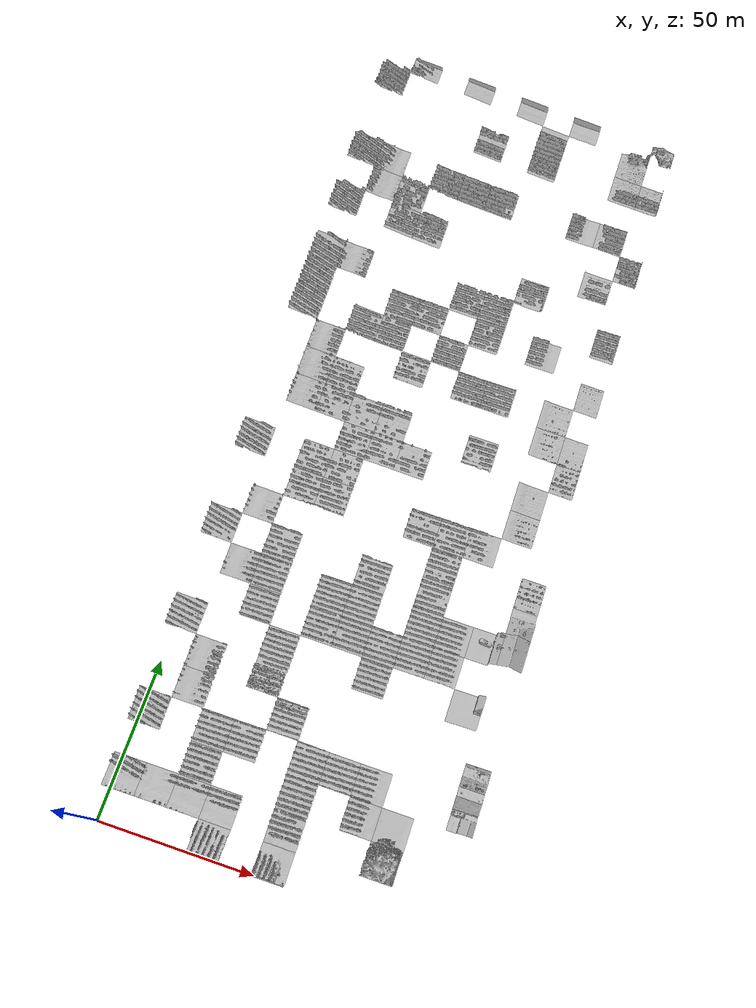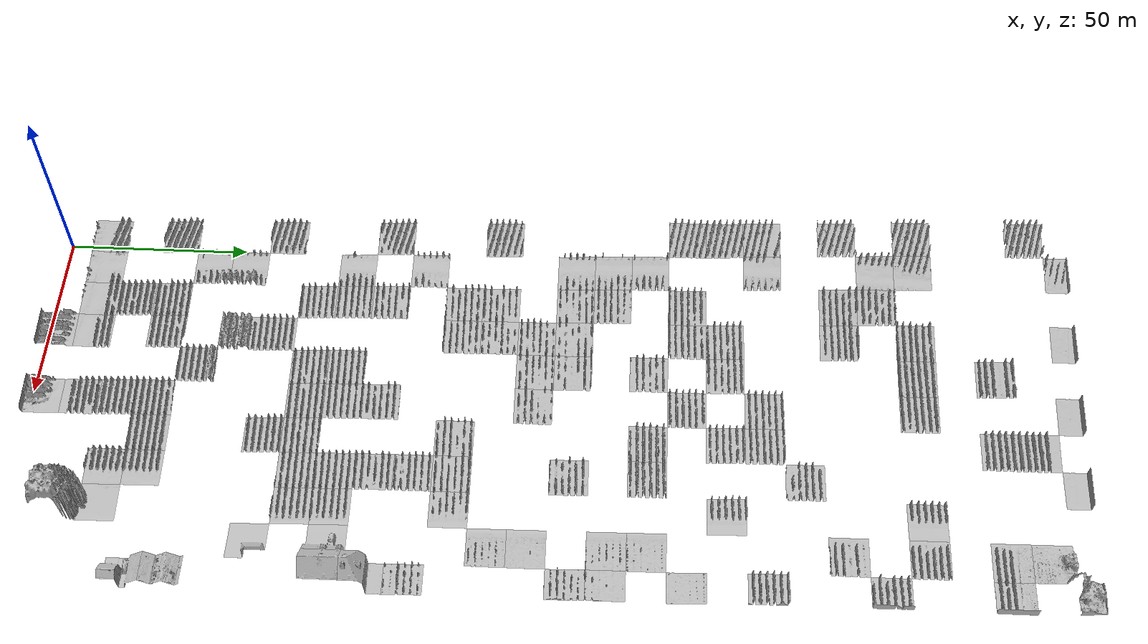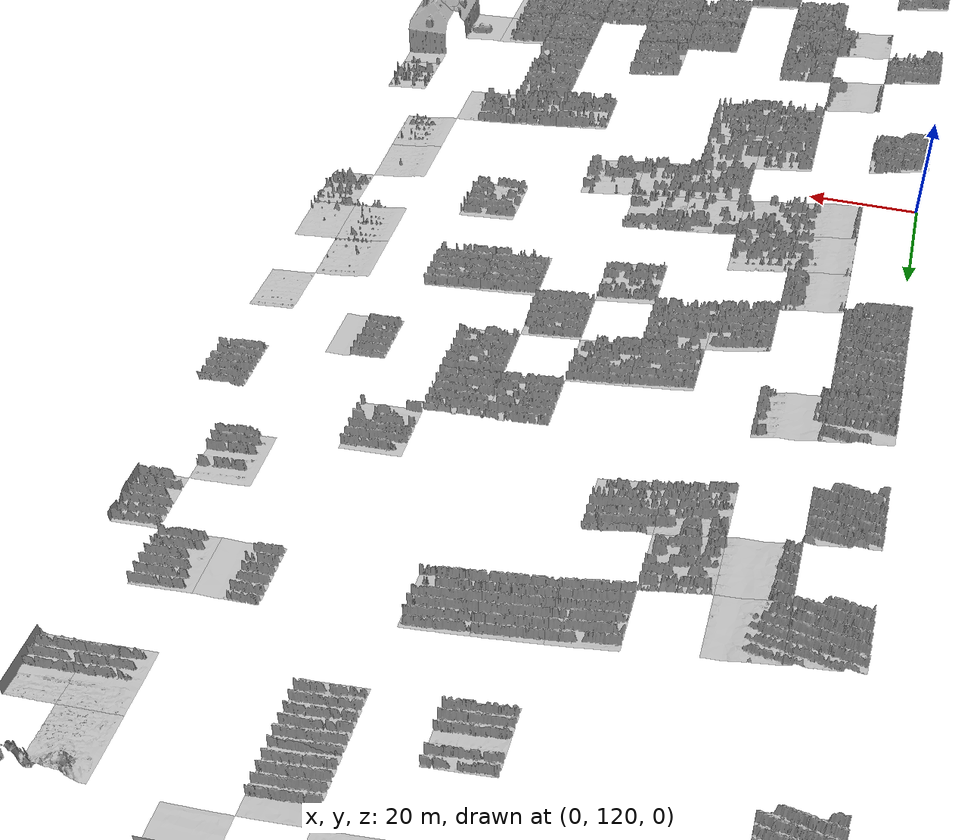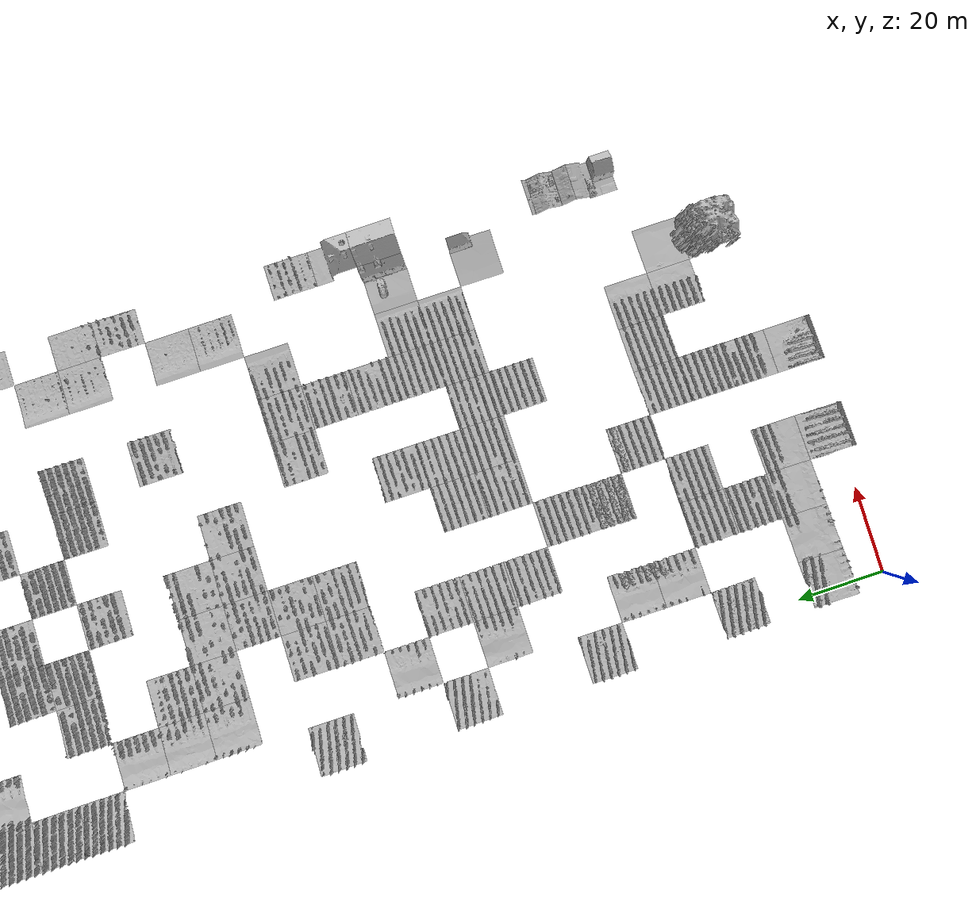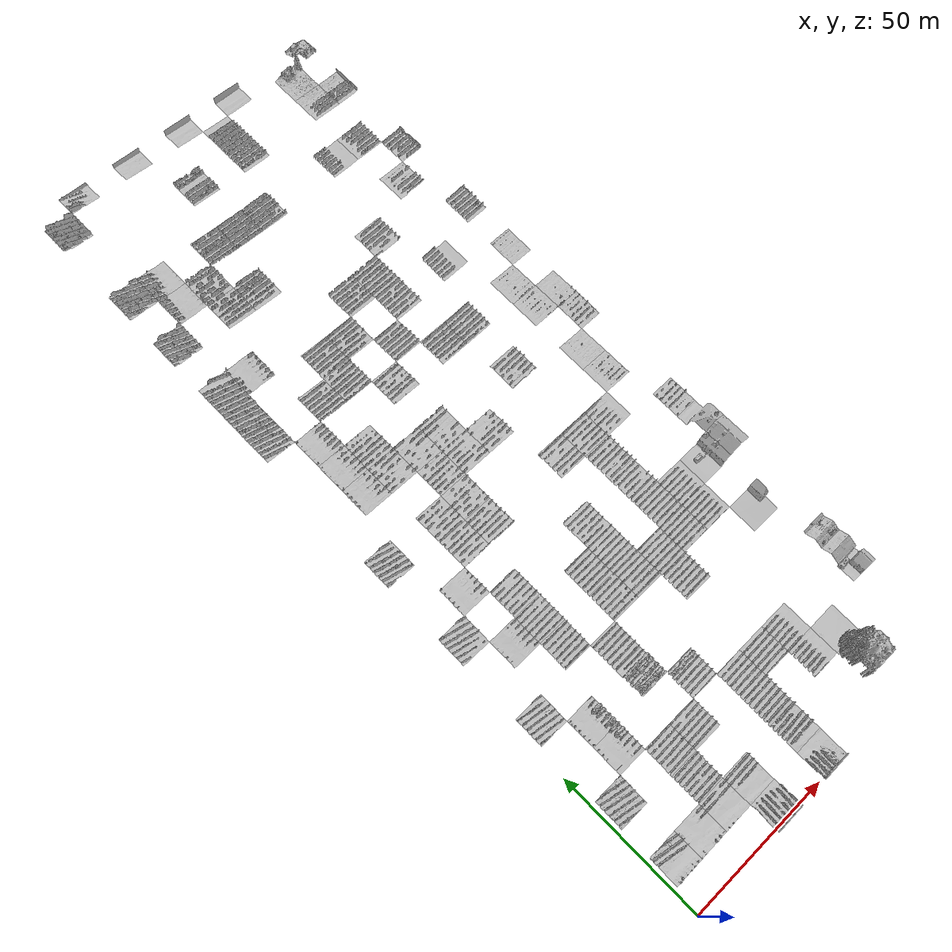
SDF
<sdf version="1.4">
 <world name="vineyard">
  <physics type="ode">
   <max_step_size>0.004</max_step_size>
   <real_time_factor>1</real_time_factor>
   <real_time_update_rate>250</real_time_update_rate>
  </physics>
  <include><uri>model://map_10_10</uri><pose>10 10 0 0 0 0</pose></include>
  <include><uri>model://map_180_40</uri><pose>40 180 0 0 0 0</pose></include>
  <include><uri>model://map_260_0</uri><pose>0 260 0 0 0 0</pose></include>
  <include><uri>model://map_70_60</uri><pose>60 70 0 0 0 0</pose></include>
  <include><uri>model://map_10_30</uri><pose>30 10 0 0 0 0</pose></include>
  <include><uri>model://map_230_80</uri><pose>80 230 0 0 0 0</pose></include>
  <include><uri>model://map_20_80</uri><pose>80 20 0 0 0 0</pose></include>
  <include><uri>model://map_160_10</uri><pose>10 160 0 0 0 0</pose></include>
  <include><uri>model://map_50_30</uri><pose>30 50 0 0 0 0</pose></include>
  <include><uri>model://map_60_90</uri><pose>90 60 0 0 0 0</pose></include>
  <include><uri>model://map_30_0</uri><pose>0 30 0 0 0 0</pose></include>
  <include><uri>model://map_30_70</uri><pose>70 30 0 0 0 0</pose></include>
  <include><uri>model://map_50_10</uri><pose>10 50 0 0 0 0</pose></include>
  <include><uri>model://map_150_20</uri><pose>20 150 0 0 0 0</pose></include>
  <include><uri>model://map_190_60</uri><pose>60 190 0 0 0 0</pose></include>
  <include><uri>model://map_150_90</uri><pose>90 150 0 0 0 0</pose></include>
  <include><uri>model://map_140_100</uri><pose>100 140 0 0 0 0</pose></include>
  <include><uri>model://map_100_10</uri><pose>10 100 0 0 0 0</pose></include>
  <include><uri>model://map_210_30</uri><pose>30 210 0 0 0 0</pose></include>
  <include><uri>model://map_130_30</uri><pose>30 130 0 0 0 0</pose></include>
  <include><uri>model://map_170_20</uri><pose>20 170 0 0 0 0</pose></include>
  <include><uri>model://map_210_20</uri><pose>20 210 0 0 0 0</pose></include>
  <include><uri>model://map_230_90</uri><pose>90 230 0 0 0 0</pose></include>
  <include><uri>model://map_0_30</uri><pose>30 0 0 0 0 0</pose></include>
  <include><uri>model://map_190_50</uri><pose>50 190 0 0 0 0</pose></include>
  <include><uri>model://map_90_70</uri><pose>70 90 0 0 0 0</pose></include>
  <include><uri>model://map_250_90</uri><pose>90 250 0 0 0 0</pose></include>
  <include><uri>model://map_80_20</uri><pose>20 80 0 0 0 0</pose></include>
  <include><uri>model://map_70_20</uri><pose>20 70 0 0 0 0</pose></include>
  <include><uri>model://map_210_90</uri><pose>90 210 0 0 0 0</pose></include>
  <include><uri>model://map_270_100</uri><pose>100 270 0 0 0 0</pose></include>
  <include><uri>model://map_180_30</uri><pose>30 180 0 0 0 0</pose></include>
  <include><uri>model://map_130_40</uri><pose>40 130 0 0 0 0</pose></include>
  <include><uri>model://map_60_60</uri><pose>60 60 0 0 0 0</pose></include>
  <include><uri>model://map_40_40</uri><pose>40 40 0 0 0 0</pose></include>
  <include><uri>model://map_140_30</uri><pose>30 140 0 0 0 0</pose></include>
  <include><uri>model://map_120_30</uri><pose>30 120 0 0 0 0</pose></include>
  <include><uri>model://map_70_40</uri><pose>40 70 0 0 0 0</pose></include>
  <include><uri>model://map_270_50</uri><pose>50 270 0 0 0 0</pose></include>
  <include><uri>model://map_260_90</uri><pose>90 260 0 0 0 0</pose></include>
  <include><uri>model://map_80_90</uri><pose>90 80 0 0 0 0</pose></include>
  <include><uri>model://map_70_70</uri><pose>70 70 0 0 0 0</pose></include>
  <include><uri>model://map_70_80</uri><pose>80 70 0 0 0 0</pose></include>
  <include><uri>model://map_180_60</uri><pose>60 180 0 0 0 0</pose></include>
  <include><uri>model://map_190_10</uri><pose>10 190 0 0 0 0</pose></include>
  <include><uri>model://map_80_10</uri><pose>10 80 0 0 0 0</pose></include>
  <include><uri>model://map_210_0</uri><pose>0 210 0 0 0 0</pose></include>
  <include><uri>model://map_220_100</uri><pose>100 220 0 0 0 0</pose></include>
  <include><uri>model://map_170_0</uri><pose>0 170 0 0 0 0</pose></include>
  <include><uri>model://map_0_50</uri><pose>50 0 0 0 0 0</pose></include>
  <include><uri>model://map_180_0</uri><pose>0 180 0 0 0 0</pose></include>
  <include><uri>model://map_270_70</uri><pose>70 270 0 0 0 0</pose></include>
  <include><uri>model://map_140_40</uri><pose>40 140 0 0 0 0</pose></include>
  <include><uri>model://map_140_20</uri><pose>20 140 0 0 0 0</pose></include>
  <include><uri>model://map_70_50</uri><pose>50 70 0 0 0 0</pose></include>
  <include><uri>model://map_130_50</uri><pose>50 130 0 0 0 0</pose></include>
  <include><uri>model://map_40_10</uri><pose>10 40 0 0 0 0</pose></include>
  <include><uri>model://map_110_60</uri><pose>60 110 0 0 0 0</pose></include>
  <include><uri>model://map_60_0</uri><pose>0 60 0 0 0 0</pose></include>
  <include><uri>model://map_120_90</uri><pose>90 120 0 0 0 0</pose></include>
  <include><uri>model://map_150_100</uri><pose>100 150 0 0 0 0</pose></include>
  <include><uri>model://map_30_20</uri><pose>20 30 0 0 0 0</pose></include>
  <include><uri>model://map_80_80</uri><pose>80 80 0 0 0 0</pose></include>
  <include><uri>model://map_90_0</uri><pose>0 90 0 0 0 0</pose></include>
  <include><uri>model://map_270_30</uri><pose>30 270 0 0 0 0</pose></include>
  <include><uri>model://map_250_100</uri><pose>100 250 0 0 0 0</pose></include>
  <include><uri>model://map_260_60</uri><pose>60 260 0 0 0 0</pose></include>
  <include><uri>model://map_20_20</uri><pose>20 20 0 0 0 0</pose></include>
  <include><uri>model://map_10_50</uri><pose>50 10 0 0 0 0</pose></include>
  <include><uri>model://map_30_60</uri><pose>60 30 0 0 0 0</pose></include>
  <include><uri>model://map_160_90</uri><pose>90 160 0 0 0 0</pose></include>
  <include><uri>model://map_170_50</uri><pose>50 170 0 0 0 0</pose></include>
  <include><uri>model://map_190_100</uri><pose>100 190 0 0 0 0</pose></include>
  <include><uri>model://map_230_50</uri><pose>50 230 0 0 0 0</pose></include>
  <include><uri>model://map_30_100</uri><pose>100 30 0 0 0 0</pose></include>
  <include><uri>model://map_60_30</uri><pose>30 60 0 0 0 0</pose></include>
  <include><uri>model://map_90_20</uri><pose>20 90 0 0 0 0</pose></include>
  <include><uri>model://map_80_100</uri><pose>100 80 0 0 0 0</pose></include>
  <include><uri>model://map_110_80</uri><pose>80 110 0 0 0 0</pose></include>
  <include><uri>model://map_20_70</uri><pose>70 20 0 0 0 0</pose></include>
  <include><uri>model://map_100_100</uri><pose>100 100 0 0 0 0</pose></include>
  <include><uri>model://map_90_50</uri><pose>50 90 0 0 0 0</pose></include>
  <include><uri>model://map_120_0</uri><pose>0 120 0 0 0 0</pose></include>
  <include><uri>model://map_140_70</uri><pose>70 140 0 0 0 0</pose></include>
  <include><uri>model://map_170_100</uri><pose>100 170 0 0 0 0</pose></include>
  <include><uri>model://map_90_100</uri><pose>100 90 0 0 0 0</pose></include>
  <include><uri>model://map_120_20</uri><pose>20 120 0 0 0 0</pose></include>
  <include><uri>model://map_160_70</uri><pose>70 160 0 0 0 0</pose></include>
  <include><uri>model://map_230_10</uri><pose>10 230 0 0 0 0</pose></include>
  <include><uri>model://map_160_40</uri><pose>40 160 0 0 0 0</pose></include>
  <include><uri>model://map_10_80</uri><pose>80 10 0 0 0 0</pose></include>
  <include><uri>model://map_140_10</uri><pose>10 140 0 0 0 0</pose></include>
  <include><uri>model://map_250_60</uri><pose>60 250 0 0 0 0</pose></include>
  <include><uri>model://map_30_30</uri><pose>30 30 0 0 0 0</pose></include>
  <include><uri>model://map_220_20</uri><pose>20 220 0 0 0 0</pose></include>
  <include><uri>model://map_230_0</uri><pose>0 230 0 0 0 0</pose></include>
  <include><uri>model://map_80_50</uri><pose>50 80 0 0 0 0</pose></include>
  <include><uri>model://map_80_40</uri><pose>40 80 0 0 0 0</pose></include>
  <include><uri>model://map_230_30</uri><pose>30 230 0 0 0 0</pose></include>
  <include><uri>model://map_10_20</uri><pose>20 10 0 0 0 0</pose></include>
  <include><uri>model://map_150_10</uri><pose>10 150 0 0 0 0</pose></include>
  <include><uri>model://map_200_70</uri><pose>70 200 0 0 0 0</pose></include>
  <include><uri>model://map_220_10</uri><pose>10 220 0 0 0 0</pose></include>
  <include><uri>model://map_180_80</uri><pose>80 180 0 0 0 0</pose></include>
  <include><uri>model://map_40_100</uri><pose>100 40 0 0 0 0</pose></include>
  <include><uri>model://map_230_40</uri><pose>40 230 0 0 0 0</pose></include>
  <include><uri>model://map_130_90</uri><pose>90 130 0 0 0 0</pose></include>
  <include><uri>model://map_110_70</uri><pose>70 110 0 0 0 0</pose></include>
  <include><uri>model://map_170_30</uri><pose>30 170 0 0 0 0</pose></include>
  <include><uri>model://map_160_60</uri><pose>60 160 0 0 0 0</pose></include>
  <include><uri>model://map_10_0</uri><pose>0 10 0 0 0 0</pose></include>
  <include><uri>model://map_100_70</uri><pose>70 100 0 0 0 0</pose></include>
  <include><uri>model://map_250_40</uri><pose>40 250 0 0 0 0</pose></include>
  <include><uri>model://map_270_10</uri><pose>10 270 0 0 0 0</pose></include>
  <include><uri>model://map_110_20</uri><pose>20 110 0 0 0 0</pose></include>
  <include><uri>model://map_30_50</uri><pose>50 30 0 0 0 0</pose></include>
  <include><uri>model://map_110_30</uri><pose>30 110 0 0 0 0</pose></include>
  <include><uri>model://map_80_70</uri><pose>70 80 0 0 0 0</pose></include>
  <include><uri>model://map_20_50</uri><pose>50 20 0 0 0 0</pose></include>
  <include><uri>model://map_190_0</uri><pose>0 190 0 0 0 0</pose></include>
  <include><uri>model://sun</uri></include>
 </world>
</sdf>

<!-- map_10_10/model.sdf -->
<sdf version="1.4">
    <model name="map_10_10">
        <link name="map_10_10_link">
            <visual name="map_10_10_visual">
                <geometry>
                    <mesh>
                        <uri>meshes/visual/map_10_10.obj</uri>
                    </mesh>
                </geometry>
            </visual>
            <collision name="map_10_10_collision">
                <surface>
                    <friction>
                        <ode>
                            <mu>2.316343837943928</mu>
                            <mu2>2.316343837943928</mu2>
                        </ode>
                        <bullet>
                            <friction>2.316343837943928</friction>
                            <friction2>2.316343837943928</friction2>
                        </bullet>
                    </friction>
                </surface>
                <geometry>
                    <mesh>
                        <uri>meshes/visual/map_10_10.obj</uri>
                    </mesh>
                </geometry>
            </collision>
        </link>
        <static>True</static>
    </model>
</sdf>

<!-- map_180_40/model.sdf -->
<sdf version="1.4">
    <model name="map_180_40">
        <link name="map_180_40_link">
            <visual name="map_180_40_visual">
                <geometry>
                    <mesh>
                        <uri>meshes/visual/map_180_40.obj</uri>
                    </mesh>
                </geometry>
            </visual>
            <collision name="map_180_40_collision">
                <surface>
                    <friction>
                        <ode>
                            <mu>2.316343837943928</mu>
                            <mu2>2.316343837943928</mu2>
                        </ode>
                        <bullet>
                            <friction>2.316343837943928</friction>
                            <friction2>2.316343837943928</friction2>
                        </bullet>
                    </friction>
                </surface>
                <geometry>
                    <mesh>
                        <uri>meshes/visual/map_180_40.obj</uri>
                    </mesh>
                </geometry>
            </collision>
        </link>
        <static>True</static>
    </model>
</sdf>

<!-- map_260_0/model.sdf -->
<sdf version="1.4">
    <model name="map_260_0">
        <link name="map_260_0_link">
            <visual name="map_260_0_visual">
                <geometry>
                    <mesh>
                        <uri>meshes/visual/map_260_0.obj</uri>
                    </mesh>
                </geometry>
            </visual>
            <collision name="map_260_0_collision">
                <surface>
                    <friction>
                        <ode>
                            <mu>2.316343837943928</mu>
                            <mu2>2.316343837943928</mu2>
                        </ode>
                        <bullet>
                            <friction>2.316343837943928</friction>
                            <friction2>2.316343837943928</friction2>
                        </bullet>
                    </friction>
                </surface>
                <geometry>
                    <mesh>
                        <uri>meshes/visual/map_260_0.obj</uri>
                    </mesh>
                </geometry>
            </collision>
        </link>
        <static>True</static>
    </model>
</sdf>

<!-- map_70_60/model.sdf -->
<sdf version="1.4">
    <model name="map_70_60">
        <link name="map_70_60_link">
            <visual name="map_70_60_visual">
                <geometry>
                    <mesh>
                        <uri>meshes/visual/map_70_60.obj</uri>
                    </mesh>
                </geometry>
            </visual>
            <collision name="map_70_60_collision">
                <surface>
                    <friction>
                        <ode>
                            <mu>2.316343837943928</mu>
                            <mu2>2.316343837943928</mu2>
                        </ode>
                        <bullet>
                            <friction>2.316343837943928</friction>
                            <friction2>2.316343837943928</friction2>
                        </bullet>
                    </friction>
                </surface>
                <geometry>
                    <mesh>
                        <uri>meshes/visual/map_70_60.obj</uri>
                    </mesh>
                </geometry>
            </collision>
        </link>
        <static>True</static>
    </model>
</sdf>

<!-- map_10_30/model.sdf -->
<sdf version="1.4">
    <model name="map_10_30">
        <link name="map_10_30_link">
            <visual name="map_10_30_visual">
                <geometry>
                    <mesh>
                        <uri>meshes/visual/map_10_30.obj</uri>
                    </mesh>
                </geometry>
            </visual>
            <collision name="map_10_30_collision">
                <surface>
                    <friction>
                        <ode>
                            <mu>2.316343837943928</mu>
                            <mu2>2.316343837943928</mu2>
                        </ode>
                        <bullet>
                            <friction>2.316343837943928</friction>
                            <friction2>2.316343837943928</friction2>
                        </bullet>
                    </friction>
                </surface>
                <geometry>
                    <mesh>
                        <uri>meshes/visual/map_10_30.obj</uri>
                    </mesh>
                </geometry>
            </collision>
        </link>
        <static>True</static>
    </model>
</sdf>

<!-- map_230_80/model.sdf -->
<sdf version="1.4">
    <model name="map_230_80">
        <link name="map_230_80_link">
            <visual name="map_230_80_visual">
                <geometry>
                    <mesh>
                        <uri>meshes/visual/map_230_80.obj</uri>
                    </mesh>
                </geometry>
            </visual>
            <collision name="map_230_80_collision">
                <surface>
                    <friction>
                        <ode>
                            <mu>2.316343837943928</mu>
                            <mu2>2.316343837943928</mu2>
                        </ode>
                        <bullet>
                            <friction>2.316343837943928</friction>
                            <friction2>2.316343837943928</friction2>
                        </bullet>
                    </friction>
                </surface>
                <geometry>
                    <mesh>
                        <uri>meshes/visual/map_230_80.obj</uri>
                    </mesh>
                </geometry>
            </collision>
        </link>
        <static>True</static>
    </model>
</sdf>

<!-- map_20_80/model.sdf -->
<sdf version="1.4">
    <model name="map_20_80">
        <link name="map_20_80_link">
            <visual name="map_20_80_visual">
                <geometry>
                    <mesh>
                        <uri>meshes/visual/map_20_80.obj</uri>
                    </mesh>
                </geometry>
            </visual>
            <collision name="map_20_80_collision">
                <surface>
                    <friction>
                        <ode>
                            <mu>2.316343837943928</mu>
                            <mu2>2.316343837943928</mu2>
                        </ode>
                        <bullet>
                            <friction>2.316343837943928</friction>
                            <friction2>2.316343837943928</friction2>
                        </bullet>
                    </friction>
                </surface>
                <geometry>
                    <mesh>
                        <uri>meshes/visual/map_20_80.obj</uri>
                    </mesh>
                </geometry>
            </collision>
        </link>
        <static>True</static>
    </model>
</sdf>

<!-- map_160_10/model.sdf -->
<sdf version="1.4">
    <model name="map_160_10">
        <link name="map_160_10_link">
            <visual name="map_160_10_visual">
                <geometry>
                    <mesh>
                        <uri>meshes/visual/map_160_10.obj</uri>
                    </mesh>
                </geometry>
            </visual>
            <collision name="map_160_10_collision">
                <surface>
                    <friction>
                        <ode>
                            <mu>2.316343837943928</mu>
                            <mu2>2.316343837943928</mu2>
                        </ode>
                        <bullet>
                            <friction>2.316343837943928</friction>
                            <friction2>2.316343837943928</friction2>
                        </bullet>
                    </friction>
                </surface>
                <geometry>
                    <mesh>
                        <uri>meshes/visual/map_160_10.obj</uri>
                    </mesh>
                </geometry>
            </collision>
        </link>
        <static>True</static>
    </model>
</sdf>

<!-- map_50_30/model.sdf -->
<sdf version="1.4">
    <model name="map_50_30">
        <link name="map_50_30_link">
            <visual name="map_50_30_visual">
                <geometry>
                    <mesh>
                        <uri>meshes/visual/map_50_30.obj</uri>
                    </mesh>
                </geometry>
            </visual>
            <collision name="map_50_30_collision">
                <surface>
                    <friction>
                        <ode>
                            <mu>2.316343837943928</mu>
                            <mu2>2.316343837943928</mu2>
                        </ode>
                        <bullet>
                            <friction>2.316343837943928</friction>
                            <friction2>2.316343837943928</friction2>
                        </bullet>
                    </friction>
                </surface>
                <geometry>
                    <mesh>
                        <uri>meshes/visual/map_50_30.obj</uri>
                    </mesh>
                </geometry>
            </collision>
        </link>
        <static>True</static>
    </model>
</sdf>

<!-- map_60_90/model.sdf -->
<sdf version="1.4">
    <model name="map_60_90">
        <link name="map_60_90_link">
            <visual name="map_60_90_visual">
                <geometry>
                    <mesh>
                        <uri>meshes/visual/map_60_90.obj</uri>
                    </mesh>
                </geometry>
            </visual>
            <collision name="map_60_90_collision">
                <surface>
                    <friction>
                        <ode>
                            <mu>2.316343837943928</mu>
                            <mu2>2.316343837943928</mu2>
                        </ode>
                        <bullet>
                            <friction>2.316343837943928</friction>
                            <friction2>2.316343837943928</friction2>
                        </bullet>
                    </friction>
                </surface>
                <geometry>
                    <mesh>
                        <uri>meshes/visual/map_60_90.obj</uri>
                    </mesh>
                </geometry>
            </collision>
        </link>
        <static>True</static>
    </model>
</sdf>

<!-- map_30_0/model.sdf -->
<sdf version="1.4">
    <model name="map_30_0">
        <link name="map_30_0_link">
            <visual name="map_30_0_visual">
                <geometry>
                    <mesh>
                        <uri>meshes/visual/map_30_0.obj</uri>
                    </mesh>
                </geometry>
            </visual>
            <collision name="map_30_0_collision">
                <surface>
                    <friction>
                        <ode>
                            <mu>2.316343837943928</mu>
                            <mu2>2.316343837943928</mu2>
                        </ode>
                        <bullet>
                            <friction>2.316343837943928</friction>
                            <friction2>2.316343837943928</friction2>
                        </bullet>
                    </friction>
                </surface>
                <geometry>
                    <mesh>
                        <uri>meshes/visual/map_30_0.obj</uri>
                    </mesh>
                </geometry>
            </collision>
        </link>
        <static>True</static>
    </model>
</sdf>

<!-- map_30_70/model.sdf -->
<sdf version="1.4">
    <model name="map_30_70">
        <link name="map_30_70_link">
            <visual name="map_30_70_visual">
                <geometry>
                    <mesh>
                        <uri>meshes/visual/map_30_70.obj</uri>
                    </mesh>
                </geometry>
            </visual>
            <collision name="map_30_70_collision">
                <surface>
                    <friction>
                        <ode>
                            <mu>2.316343837943928</mu>
                            <mu2>2.316343837943928</mu2>
                        </ode>
                        <bullet>
                            <friction>2.316343837943928</friction>
                            <friction2>2.316343837943928</friction2>
                        </bullet>
                    </friction>
                </surface>
                <geometry>
                    <mesh>
                        <uri>meshes/visual/map_30_70.obj</uri>
                    </mesh>
                </geometry>
            </collision>
        </link>
        <static>True</static>
    </model>
</sdf>

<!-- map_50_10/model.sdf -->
<sdf version="1.4">
    <model name="map_50_10">
        <link name="map_50_10_link">
            <visual name="map_50_10_visual">
                <geometry>
                    <mesh>
                        <uri>meshes/visual/map_50_10.obj</uri>
                    </mesh>
                </geometry>
            </visual>
            <collision name="map_50_10_collision">
                <surface>
                    <friction>
                        <ode>
                            <mu>2.316343837943928</mu>
                            <mu2>2.316343837943928</mu2>
                        </ode>
                        <bullet>
                            <friction>2.316343837943928</friction>
                            <friction2>2.316343837943928</friction2>
                        </bullet>
                    </friction>
                </surface>
                <geometry>
                    <mesh>
                        <uri>meshes/visual/map_50_10.obj</uri>
                    </mesh>
                </geometry>
            </collision>
        </link>
        <static>True</static>
    </model>
</sdf>

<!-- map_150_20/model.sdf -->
<sdf version="1.4">
    <model name="map_150_20">
        <link name="map_150_20_link">
            <visual name="map_150_20_visual">
                <geometry>
                    <mesh>
                        <uri>meshes/visual/map_150_20.obj</uri>
                    </mesh>
                </geometry>
            </visual>
            <collision name="map_150_20_collision">
                <surface>
                    <friction>
                        <ode>
                            <mu>2.316343837943928</mu>
                            <mu2>2.316343837943928</mu2>
                        </ode>
                        <bullet>
                            <friction>2.316343837943928</friction>
                            <friction2>2.316343837943928</friction2>
                        </bullet>
                    </friction>
                </surface>
                <geometry>
                    <mesh>
                        <uri>meshes/visual/map_150_20.obj</uri>
                    </mesh>
                </geometry>
            </collision>
        </link>
        <static>True</static>
    </model>
</sdf>

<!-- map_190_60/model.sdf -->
<sdf version="1.4">
    <model name="map_190_60">
        <link name="map_190_60_link">
            <visual name="map_190_60_visual">
                <geometry>
                    <mesh>
                        <uri>meshes/visual/map_190_60.obj</uri>
                    </mesh>
                </geometry>
            </visual>
            <collision name="map_190_60_collision">
                <surface>
                    <friction>
                        <ode>
                            <mu>2.316343837943928</mu>
                            <mu2>2.316343837943928</mu2>
                        </ode>
                        <bullet>
                            <friction>2.316343837943928</friction>
                            <friction2>2.316343837943928</friction2>
                        </bullet>
                    </friction>
                </surface>
                <geometry>
                    <mesh>
                        <uri>meshes/visual/map_190_60.obj</uri>
                    </mesh>
                </geometry>
            </collision>
        </link>
        <static>True</static>
    </model>
</sdf>

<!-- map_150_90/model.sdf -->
<sdf version="1.4">
    <model name="map_150_90">
        <link name="map_150_90_link">
            <visual name="map_150_90_visual">
                <geometry>
                    <mesh>
                        <uri>meshes/visual/map_150_90.obj</uri>
                    </mesh>
                </geometry>
            </visual>
            <collision name="map_150_90_collision">
                <surface>
                    <friction>
                        <ode>
                            <mu>2.316343837943928</mu>
                            <mu2>2.316343837943928</mu2>
                        </ode>
                        <bullet>
                            <friction>2.316343837943928</friction>
                            <friction2>2.316343837943928</friction2>
                        </bullet>
                    </friction>
                </surface>
                <geometry>
                    <mesh>
                        <uri>meshes/visual/map_150_90.obj</uri>
                    </mesh>
                </geometry>
            </collision>
        </link>
        <static>True</static>
    </model>
</sdf>

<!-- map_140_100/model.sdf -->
<sdf version="1.4">
    <model name="map_140_100">
        <link name="map_140_100_link">
            <visual name="map_140_100_visual">
                <geometry>
                    <mesh>
                        <uri>meshes/visual/map_140_100.obj</uri>
                    </mesh>
                </geometry>
            </visual>
            <collision name="map_140_100_collision">
                <surface>
                    <friction>
                        <ode>
                            <mu>2.316343837943928</mu>
                            <mu2>2.316343837943928</mu2>
                        </ode>
                        <bullet>
                            <friction>2.316343837943928</friction>
                            <friction2>2.316343837943928</friction2>
                        </bullet>
                    </friction>
                </surface>
                <geometry>
                    <mesh>
                        <uri>meshes/visual/map_140_100.obj</uri>
                    </mesh>
                </geometry>
            </collision>
        </link>
        <static>True</static>
    </model>
</sdf>

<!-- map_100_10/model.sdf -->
<sdf version="1.4">
    <model name="map_100_10">
        <link name="map_100_10_link">
            <visual name="map_100_10_visual">
                <geometry>
                    <mesh>
                        <uri>meshes/visual/map_100_10.obj</uri>
                    </mesh>
                </geometry>
            </visual>
            <collision name="map_100_10_collision">
                <surface>
                    <friction>
                        <ode>
                            <mu>2.316343837943928</mu>
                            <mu2>2.316343837943928</mu2>
                        </ode>
                        <bullet>
                            <friction>2.316343837943928</friction>
                            <friction2>2.316343837943928</friction2>
                        </bullet>
                    </friction>
                </surface>
                <geometry>
                    <mesh>
                        <uri>meshes/visual/map_100_10.obj</uri>
                    </mesh>
                </geometry>
            </collision>
        </link>
        <static>True</static>
    </model>
</sdf>

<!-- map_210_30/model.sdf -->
<sdf version="1.4">
    <model name="map_210_30">
        <link name="map_210_30_link">
            <visual name="map_210_30_visual">
                <geometry>
                    <mesh>
                        <uri>meshes/visual/map_210_30.obj</uri>
                    </mesh>
                </geometry>
            </visual>
            <collision name="map_210_30_collision">
                <surface>
                    <friction>
                        <ode>
                            <mu>2.316343837943928</mu>
                            <mu2>2.316343837943928</mu2>
                        </ode>
                        <bullet>
                            <friction>2.316343837943928</friction>
                            <friction2>2.316343837943928</friction2>
                        </bullet>
                    </friction>
                </surface>
                <geometry>
                    <mesh>
                        <uri>meshes/visual/map_210_30.obj</uri>
                    </mesh>
                </geometry>
            </collision>
        </link>
        <static>True</static>
    </model>
</sdf>

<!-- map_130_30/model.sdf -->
<sdf version="1.4">
    <model name="map_130_30">
        <link name="map_130_30_link">
            <visual name="map_130_30_visual">
                <geometry>
                    <mesh>
                        <uri>meshes/visual/map_130_30.obj</uri>
                    </mesh>
                </geometry>
            </visual>
            <collision name="map_130_30_collision">
                <surface>
                    <friction>
                        <ode>
                            <mu>2.316343837943928</mu>
                            <mu2>2.316343837943928</mu2>
                        </ode>
                        <bullet>
                            <friction>2.316343837943928</friction>
                            <friction2>2.316343837943928</friction2>
                        </bullet>
                    </friction>
                </surface>
                <geometry>
                    <mesh>
                        <uri>meshes/visual/map_130_30.obj</uri>
                    </mesh>
                </geometry>
            </collision>
        </link>
        <static>True</static>
    </model>
</sdf>

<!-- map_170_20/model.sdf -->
<sdf version="1.4">
    <model name="map_170_20">
        <link name="map_170_20_link">
            <visual name="map_170_20_visual">
                <geometry>
                    <mesh>
                        <uri>meshes/visual/map_170_20.obj</uri>
                    </mesh>
                </geometry>
            </visual>
            <collision name="map_170_20_collision">
                <surface>
                    <friction>
                        <ode>
                            <mu>2.316343837943928</mu>
                            <mu2>2.316343837943928</mu2>
                        </ode>
                        <bullet>
                            <friction>2.316343837943928</friction>
                            <friction2>2.316343837943928</friction2>
                        </bullet>
                    </friction>
                </surface>
                <geometry>
                    <mesh>
                        <uri>meshes/visual/map_170_20.obj</uri>
                    </mesh>
                </geometry>
            </collision>
        </link>
        <static>True</static>
    </model>
</sdf>

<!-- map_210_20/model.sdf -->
<sdf version="1.4">
    <model name="map_210_20">
        <link name="map_210_20_link">
            <visual name="map_210_20_visual">
                <geometry>
                    <mesh>
                        <uri>meshes/visual/map_210_20.obj</uri>
                    </mesh>
                </geometry>
            </visual>
            <collision name="map_210_20_collision">
                <surface>
                    <friction>
                        <ode>
                            <mu>2.316343837943928</mu>
                            <mu2>2.316343837943928</mu2>
                        </ode>
                        <bullet>
                            <friction>2.316343837943928</friction>
                            <friction2>2.316343837943928</friction2>
                        </bullet>
                    </friction>
                </surface>
                <geometry>
                    <mesh>
                        <uri>meshes/visual/map_210_20.obj</uri>
                    </mesh>
                </geometry>
            </collision>
        </link>
        <static>True</static>
    </model>
</sdf>

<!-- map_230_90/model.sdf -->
<sdf version="1.4">
    <model name="map_230_90">
        <link name="map_230_90_link">
            <visual name="map_230_90_visual">
                <geometry>
                    <mesh>
                        <uri>meshes/visual/map_230_90.obj</uri>
                    </mesh>
                </geometry>
            </visual>
            <collision name="map_230_90_collision">
                <surface>
                    <friction>
                        <ode>
                            <mu>2.316343837943928</mu>
                            <mu2>2.316343837943928</mu2>
                        </ode>
                        <bullet>
                            <friction>2.316343837943928</friction>
                            <friction2>2.316343837943928</friction2>
                        </bullet>
                    </friction>
                </surface>
                <geometry>
                    <mesh>
                        <uri>meshes/visual/map_230_90.obj</uri>
                    </mesh>
                </geometry>
            </collision>
        </link>
        <static>True</static>
    </model>
</sdf>

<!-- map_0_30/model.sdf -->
<sdf version="1.4">
    <model name="map_0_30">
        <link name="map_0_30_link">
            <visual name="map_0_30_visual">
                <geometry>
                    <mesh>
                        <uri>meshes/visual/map_0_30.obj</uri>
                    </mesh>
                </geometry>
            </visual>
            <collision name="map_0_30_collision">
                <surface>
                    <friction>
                        <ode>
                            <mu>2.316343837943928</mu>
                            <mu2>2.316343837943928</mu2>
                        </ode>
                        <bullet>
                            <friction>2.316343837943928</friction>
                            <friction2>2.316343837943928</friction2>
                        </bullet>
                    </friction>
                </surface>
                <geometry>
                    <mesh>
                        <uri>meshes/visual/map_0_30.obj</uri>
                    </mesh>
                </geometry>
            </collision>
        </link>
        <static>True</static>
    </model>
</sdf>

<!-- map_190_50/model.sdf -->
<sdf version="1.4">
    <model name="map_190_50">
        <link name="map_190_50_link">
            <visual name="map_190_50_visual">
                <geometry>
                    <mesh>
                        <uri>meshes/visual/map_190_50.obj</uri>
                    </mesh>
                </geometry>
            </visual>
            <collision name="map_190_50_collision">
                <surface>
                    <friction>
                        <ode>
                            <mu>2.316343837943928</mu>
                            <mu2>2.316343837943928</mu2>
                        </ode>
                        <bullet>
                            <friction>2.316343837943928</friction>
                            <friction2>2.316343837943928</friction2>
                        </bullet>
                    </friction>
                </surface>
                <geometry>
                    <mesh>
                        <uri>meshes/visual/map_190_50.obj</uri>
                    </mesh>
                </geometry>
            </collision>
        </link>
        <static>True</static>
    </model>
</sdf>

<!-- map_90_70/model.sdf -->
<sdf version="1.4">
    <model name="map_90_70">
        <link name="map_90_70_link">
            <visual name="map_90_70_visual">
                <geometry>
                    <mesh>
                        <uri>meshes/visual/map_90_70.obj</uri>
                    </mesh>
                </geometry>
            </visual>
            <collision name="map_90_70_collision">
                <surface>
                    <friction>
                        <ode>
                            <mu>2.316343837943928</mu>
                            <mu2>2.316343837943928</mu2>
                        </ode>
                        <bullet>
                            <friction>2.316343837943928</friction>
                            <friction2>2.316343837943928</friction2>
                        </bullet>
                    </friction>
                </surface>
                <geometry>
                    <mesh>
                        <uri>meshes/visual/map_90_70.obj</uri>
                    </mesh>
                </geometry>
            </collision>
        </link>
        <static>True</static>
    </model>
</sdf>

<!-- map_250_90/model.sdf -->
<sdf version="1.4">
    <model name="map_250_90">
        <link name="map_250_90_link">
            <visual name="map_250_90_visual">
                <geometry>
                    <mesh>
                        <uri>meshes/visual/map_250_90.obj</uri>
                    </mesh>
                </geometry>
            </visual>
            <collision name="map_250_90_collision">
                <surface>
                    <friction>
                        <ode>
                            <mu>2.316343837943928</mu>
                            <mu2>2.316343837943928</mu2>
                        </ode>
                        <bullet>
                            <friction>2.316343837943928</friction>
                            <friction2>2.316343837943928</friction2>
                        </bullet>
                    </friction>
                </surface>
                <geometry>
                    <mesh>
                        <uri>meshes/visual/map_250_90.obj</uri>
                    </mesh>
                </geometry>
            </collision>
        </link>
        <static>True</static>
    </model>
</sdf>

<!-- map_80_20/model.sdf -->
<sdf version="1.4">
    <model name="map_80_20">
        <link name="map_80_20_link">
            <visual name="map_80_20_visual">
                <geometry>
                    <mesh>
                        <uri>meshes/visual/map_80_20.obj</uri>
                    </mesh>
                </geometry>
            </visual>
            <collision name="map_80_20_collision">
                <surface>
                    <friction>
                        <ode>
                            <mu>2.316343837943928</mu>
                            <mu2>2.316343837943928</mu2>
                        </ode>
                        <bullet>
                            <friction>2.316343837943928</friction>
                            <friction2>2.316343837943928</friction2>
                        </bullet>
                    </friction>
                </surface>
                <geometry>
                    <mesh>
                        <uri>meshes/visual/map_80_20.obj</uri>
                    </mesh>
                </geometry>
            </collision>
        </link>
        <static>True</static>
    </model>
</sdf>

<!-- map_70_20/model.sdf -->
<sdf version="1.4">
    <model name="map_70_20">
        <link name="map_70_20_link">
            <visual name="map_70_20_visual">
                <geometry>
                    <mesh>
                        <uri>meshes/visual/map_70_20.obj</uri>
                    </mesh>
                </geometry>
            </visual>
            <collision name="map_70_20_collision">
                <surface>
                    <friction>
                        <ode>
                            <mu>2.316343837943928</mu>
                            <mu2>2.316343837943928</mu2>
                        </ode>
                        <bullet>
                            <friction>2.316343837943928</friction>
                            <friction2>2.316343837943928</friction2>
                        </bullet>
                    </friction>
                </surface>
                <geometry>
                    <mesh>
                        <uri>meshes/visual/map_70_20.obj</uri>
                    </mesh>
                </geometry>
            </collision>
        </link>
        <static>True</static>
    </model>
</sdf>

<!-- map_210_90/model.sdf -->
<sdf version="1.4">
    <model name="map_210_90">
        <link name="map_210_90_link">
            <visual name="map_210_90_visual">
                <geometry>
                    <mesh>
                        <uri>meshes/visual/map_210_90.obj</uri>
                    </mesh>
                </geometry>
            </visual>
            <collision name="map_210_90_collision">
                <surface>
                    <friction>
                        <ode>
                            <mu>2.316343837943928</mu>
                            <mu2>2.316343837943928</mu2>
                        </ode>
                        <bullet>
                            <friction>2.316343837943928</friction>
                            <friction2>2.316343837943928</friction2>
                        </bullet>
                    </friction>
                </surface>
                <geometry>
                    <mesh>
                        <uri>meshes/visual/map_210_90.obj</uri>
                    </mesh>
                </geometry>
            </collision>
        </link>
        <static>True</static>
    </model>
</sdf>

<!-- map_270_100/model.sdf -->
<sdf version="1.4">
    <model name="map_270_100">
        <link name="map_270_100_link">
            <visual name="map_270_100_visual">
                <geometry>
                    <mesh>
                        <uri>meshes/visual/map_270_100.obj</uri>
                    </mesh>
                </geometry>
            </visual>
            <collision name="map_270_100_collision">
                <surface>
                    <friction>
                        <ode>
                            <mu>2.316343837943928</mu>
                            <mu2>2.316343837943928</mu2>
                        </ode>
                        <bullet>
                            <friction>2.316343837943928</friction>
                            <friction2>2.316343837943928</friction2>
                        </bullet>
                    </friction>
                </surface>
                <geometry>
                    <mesh>
                        <uri>meshes/visual/map_270_100.obj</uri>
                    </mesh>
                </geometry>
            </collision>
        </link>
        <static>True</static>
    </model>
</sdf>

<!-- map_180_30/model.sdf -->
<sdf version="1.4">
    <model name="map_180_30">
        <link name="map_180_30_link">
            <visual name="map_180_30_visual">
                <geometry>
                    <mesh>
                        <uri>meshes/visual/map_180_30.obj</uri>
                    </mesh>
                </geometry>
            </visual>
            <collision name="map_180_30_collision">
                <surface>
                    <friction>
                        <ode>
                            <mu>2.316343837943928</mu>
                            <mu2>2.316343837943928</mu2>
                        </ode>
                        <bullet>
                            <friction>2.316343837943928</friction>
                            <friction2>2.316343837943928</friction2>
                        </bullet>
                    </friction>
                </surface>
                <geometry>
                    <mesh>
                        <uri>meshes/visual/map_180_30.obj</uri>
                    </mesh>
                </geometry>
            </collision>
        </link>
        <static>True</static>
    </model>
</sdf>

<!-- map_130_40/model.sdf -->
<sdf version="1.4">
    <model name="map_130_40">
        <link name="map_130_40_link">
            <visual name="map_130_40_visual">
                <geometry>
                    <mesh>
                        <uri>meshes/visual/map_130_40.obj</uri>
                    </mesh>
                </geometry>
            </visual>
            <collision name="map_130_40_collision">
                <surface>
                    <friction>
                        <ode>
                            <mu>2.316343837943928</mu>
                            <mu2>2.316343837943928</mu2>
                        </ode>
                        <bullet>
                            <friction>2.316343837943928</friction>
                            <friction2>2.316343837943928</friction2>
                        </bullet>
                    </friction>
                </surface>
                <geometry>
                    <mesh>
                        <uri>meshes/visual/map_130_40.obj</uri>
                    </mesh>
                </geometry>
            </collision>
        </link>
        <static>True</static>
    </model>
</sdf>

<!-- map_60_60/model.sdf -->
<sdf version="1.4">
    <model name="map_60_60">
        <link name="map_60_60_link">
            <visual name="map_60_60_visual">
                <geometry>
                    <mesh>
                        <uri>meshes/visual/map_60_60.obj</uri>
                    </mesh>
                </geometry>
            </visual>
            <collision name="map_60_60_collision">
                <surface>
                    <friction>
                        <ode>
                            <mu>2.316343837943928</mu>
                            <mu2>2.316343837943928</mu2>
                        </ode>
                        <bullet>
                            <friction>2.316343837943928</friction>
                            <friction2>2.316343837943928</friction2>
                        </bullet>
                    </friction>
                </surface>
                <geometry>
                    <mesh>
                        <uri>meshes/visual/map_60_60.obj</uri>
                    </mesh>
                </geometry>
            </collision>
        </link>
        <static>True</static>
    </model>
</sdf>

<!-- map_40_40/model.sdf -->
<sdf version="1.4">
    <model name="map_40_40">
        <link name="map_40_40_link">
            <visual name="map_40_40_visual">
                <geometry>
                    <mesh>
                        <uri>meshes/visual/map_40_40.obj</uri>
                    </mesh>
                </geometry>
            </visual>
            <collision name="map_40_40_collision">
                <surface>
                    <friction>
                        <ode>
                            <mu>2.316343837943928</mu>
                            <mu2>2.316343837943928</mu2>
                        </ode>
                        <bullet>
                            <friction>2.316343837943928</friction>
                            <friction2>2.316343837943928</friction2>
                        </bullet>
                    </friction>
                </surface>
                <geometry>
                    <mesh>
                        <uri>meshes/visual/map_40_40.obj</uri>
                    </mesh>
                </geometry>
            </collision>
        </link>
        <static>True</static>
    </model>
</sdf>

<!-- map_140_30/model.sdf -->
<sdf version="1.4">
    <model name="map_140_30">
        <link name="map_140_30_link">
            <visual name="map_140_30_visual">
                <geometry>
                    <mesh>
                        <uri>meshes/visual/map_140_30.obj</uri>
                    </mesh>
                </geometry>
            </visual>
            <collision name="map_140_30_collision">
                <surface>
                    <friction>
                        <ode>
                            <mu>2.316343837943928</mu>
                            <mu2>2.316343837943928</mu2>
                        </ode>
                        <bullet>
                            <friction>2.316343837943928</friction>
                            <friction2>2.316343837943928</friction2>
                        </bullet>
                    </friction>
                </surface>
                <geometry>
                    <mesh>
                        <uri>meshes/visual/map_140_30.obj</uri>
                    </mesh>
                </geometry>
            </collision>
        </link>
        <static>True</static>
    </model>
</sdf>

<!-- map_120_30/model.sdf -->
<sdf version="1.4">
    <model name="map_120_30">
        <link name="map_120_30_link">
            <visual name="map_120_30_visual">
                <geometry>
                    <mesh>
                        <uri>meshes/visual/map_120_30.obj</uri>
                    </mesh>
                </geometry>
            </visual>
            <collision name="map_120_30_collision">
                <surface>
                    <friction>
                        <ode>
                            <mu>2.316343837943928</mu>
                            <mu2>2.316343837943928</mu2>
                        </ode>
                        <bullet>
                            <friction>2.316343837943928</friction>
                            <friction2>2.316343837943928</friction2>
                        </bullet>
                    </friction>
                </surface>
                <geometry>
                    <mesh>
                        <uri>meshes/visual/map_120_30.obj</uri>
                    </mesh>
                </geometry>
            </collision>
        </link>
        <static>True</static>
    </model>
</sdf>

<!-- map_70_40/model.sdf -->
<sdf version="1.4">
    <model name="map_70_40">
        <link name="map_70_40_link">
            <visual name="map_70_40_visual">
                <geometry>
                    <mesh>
                        <uri>meshes/visual/map_70_40.obj</uri>
                    </mesh>
                </geometry>
            </visual>
            <collision name="map_70_40_collision">
                <surface>
                    <friction>
                        <ode>
                            <mu>2.316343837943928</mu>
                            <mu2>2.316343837943928</mu2>
                        </ode>
                        <bullet>
                            <friction>2.316343837943928</friction>
                            <friction2>2.316343837943928</friction2>
                        </bullet>
                    </friction>
                </surface>
                <geometry>
                    <mesh>
                        <uri>meshes/visual/map_70_40.obj</uri>
                    </mesh>
                </geometry>
            </collision>
        </link>
        <static>True</static>
    </model>
</sdf>

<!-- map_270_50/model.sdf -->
<sdf version="1.4">
    <model name="map_270_50">
        <link name="map_270_50_link">
            <visual name="map_270_50_visual">
                <geometry>
                    <mesh>
                        <uri>meshes/visual/map_270_50.obj</uri>
                    </mesh>
                </geometry>
            </visual>
            <collision name="map_270_50_collision">
                <surface>
                    <friction>
                        <ode>
                            <mu>2.316343837943928</mu>
                            <mu2>2.316343837943928</mu2>
                        </ode>
                        <bullet>
                            <friction>2.316343837943928</friction>
                            <friction2>2.316343837943928</friction2>
                        </bullet>
                    </friction>
                </surface>
                <geometry>
                    <mesh>
                        <uri>meshes/visual/map_270_50.obj</uri>
                    </mesh>
                </geometry>
            </collision>
        </link>
        <static>True</static>
    </model>
</sdf>

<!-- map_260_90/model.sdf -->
<sdf version="1.4">
    <model name="map_260_90">
        <link name="map_260_90_link">
            <visual name="map_260_90_visual">
                <geometry>
                    <mesh>
                        <uri>meshes/visual/map_260_90.obj</uri>
                    </mesh>
                </geometry>
            </visual>
            <collision name="map_260_90_collision">
                <surface>
                    <friction>
                        <ode>
                            <mu>2.316343837943928</mu>
                            <mu2>2.316343837943928</mu2>
                        </ode>
                        <bullet>
                            <friction>2.316343837943928</friction>
                            <friction2>2.316343837943928</friction2>
                        </bullet>
                    </friction>
                </surface>
                <geometry>
                    <mesh>
                        <uri>meshes/visual/map_260_90.obj</uri>
                    </mesh>
                </geometry>
            </collision>
        </link>
        <static>True</static>
    </model>
</sdf>

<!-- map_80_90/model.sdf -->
<sdf version="1.4">
    <model name="map_80_90">
        <link name="map_80_90_link">
            <visual name="map_80_90_visual">
                <geometry>
                    <mesh>
                        <uri>meshes/visual/map_80_90.obj</uri>
                    </mesh>
                </geometry>
            </visual>
            <collision name="map_80_90_collision">
                <surface>
                    <friction>
                        <ode>
                            <mu>2.316343837943928</mu>
                            <mu2>2.316343837943928</mu2>
                        </ode>
                        <bullet>
                            <friction>2.316343837943928</friction>
                            <friction2>2.316343837943928</friction2>
                        </bullet>
                    </friction>
                </surface>
                <geometry>
                    <mesh>
                        <uri>meshes/visual/map_80_90.obj</uri>
                    </mesh>
                </geometry>
            </collision>
        </link>
        <static>True</static>
    </model>
</sdf>

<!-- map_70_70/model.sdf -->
<sdf version="1.4">
    <model name="map_70_70">
        <link name="map_70_70_link">
            <visual name="map_70_70_visual">
                <geometry>
                    <mesh>
                        <uri>meshes/visual/map_70_70.obj</uri>
                    </mesh>
                </geometry>
            </visual>
            <collision name="map_70_70_collision">
                <surface>
                    <friction>
                        <ode>
                            <mu>2.316343837943928</mu>
                            <mu2>2.316343837943928</mu2>
                        </ode>
                        <bullet>
                            <friction>2.316343837943928</friction>
                            <friction2>2.316343837943928</friction2>
                        </bullet>
                    </friction>
                </surface>
                <geometry>
                    <mesh>
                        <uri>meshes/visual/map_70_70.obj</uri>
                    </mesh>
                </geometry>
            </collision>
        </link>
        <static>True</static>
    </model>
</sdf>

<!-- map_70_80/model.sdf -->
<sdf version="1.4">
    <model name="map_70_80">
        <link name="map_70_80_link">
            <visual name="map_70_80_visual">
                <geometry>
                    <mesh>
                        <uri>meshes/visual/map_70_80.obj</uri>
                    </mesh>
                </geometry>
            </visual>
            <collision name="map_70_80_collision">
                <surface>
                    <friction>
                        <ode>
                            <mu>2.316343837943928</mu>
                            <mu2>2.316343837943928</mu2>
                        </ode>
                        <bullet>
                            <friction>2.316343837943928</friction>
                            <friction2>2.316343837943928</friction2>
                        </bullet>
                    </friction>
                </surface>
                <geometry>
                    <mesh>
                        <uri>meshes/visual/map_70_80.obj</uri>
                    </mesh>
                </geometry>
            </collision>
        </link>
        <static>True</static>
    </model>
</sdf>

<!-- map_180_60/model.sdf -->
<sdf version="1.4">
    <model name="map_180_60">
        <link name="map_180_60_link">
            <visual name="map_180_60_visual">
                <geometry>
                    <mesh>
                        <uri>meshes/visual/map_180_60.obj</uri>
                    </mesh>
                </geometry>
            </visual>
            <collision name="map_180_60_collision">
                <surface>
                    <friction>
                        <ode>
                            <mu>2.316343837943928</mu>
                            <mu2>2.316343837943928</mu2>
                        </ode>
                        <bullet>
                            <friction>2.316343837943928</friction>
                            <friction2>2.316343837943928</friction2>
                        </bullet>
                    </friction>
                </surface>
                <geometry>
                    <mesh>
                        <uri>meshes/visual/map_180_60.obj</uri>
                    </mesh>
                </geometry>
            </collision>
        </link>
        <static>True</static>
    </model>
</sdf>

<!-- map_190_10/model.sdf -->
<sdf version="1.4">
    <model name="map_190_10">
        <link name="map_190_10_link">
            <visual name="map_190_10_visual">
                <geometry>
                    <mesh>
                        <uri>meshes/visual/map_190_10.obj</uri>
                    </mesh>
                </geometry>
            </visual>
            <collision name="map_190_10_collision">
                <surface>
                    <friction>
                        <ode>
                            <mu>2.316343837943928</mu>
                            <mu2>2.316343837943928</mu2>
                        </ode>
                        <bullet>
                            <friction>2.316343837943928</friction>
                            <friction2>2.316343837943928</friction2>
                        </bullet>
                    </friction>
                </surface>
                <geometry>
                    <mesh>
                        <uri>meshes/visual/map_190_10.obj</uri>
                    </mesh>
                </geometry>
            </collision>
        </link>
        <static>True</static>
    </model>
</sdf>

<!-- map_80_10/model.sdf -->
<sdf version="1.4">
    <model name="map_80_10">
        <link name="map_80_10_link">
            <visual name="map_80_10_visual">
                <geometry>
                    <mesh>
                        <uri>meshes/visual/map_80_10.obj</uri>
                    </mesh>
                </geometry>
            </visual>
            <collision name="map_80_10_collision">
                <surface>
                    <friction>
                        <ode>
                            <mu>2.316343837943928</mu>
                            <mu2>2.316343837943928</mu2>
                        </ode>
                        <bullet>
                            <friction>2.316343837943928</friction>
                            <friction2>2.316343837943928</friction2>
                        </bullet>
                    </friction>
                </surface>
                <geometry>
                    <mesh>
                        <uri>meshes/visual/map_80_10.obj</uri>
                    </mesh>
                </geometry>
            </collision>
        </link>
        <static>True</static>
    </model>
</sdf>

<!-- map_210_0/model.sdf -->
<sdf version="1.4">
    <model name="map_210_0">
        <link name="map_210_0_link">
            <visual name="map_210_0_visual">
                <geometry>
                    <mesh>
                        <uri>meshes/visual/map_210_0.obj</uri>
                    </mesh>
                </geometry>
            </visual>
            <collision name="map_210_0_collision">
                <surface>
                    <friction>
                        <ode>
                            <mu>2.316343837943928</mu>
                            <mu2>2.316343837943928</mu2>
                        </ode>
                        <bullet>
                            <friction>2.316343837943928</friction>
                            <friction2>2.316343837943928</friction2>
                        </bullet>
                    </friction>
                </surface>
                <geometry>
                    <mesh>
                        <uri>meshes/visual/map_210_0.obj</uri>
                    </mesh>
                </geometry>
            </collision>
        </link>
        <static>True</static>
    </model>
</sdf>

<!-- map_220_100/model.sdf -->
<sdf version="1.4">
    <model name="map_220_100">
        <link name="map_220_100_link">
            <visual name="map_220_100_visual">
                <geometry>
                    <mesh>
                        <uri>meshes/visual/map_220_100.obj</uri>
                    </mesh>
                </geometry>
            </visual>
            <collision name="map_220_100_collision">
                <surface>
                    <friction>
                        <ode>
                            <mu>2.316343837943928</mu>
                            <mu2>2.316343837943928</mu2>
                        </ode>
                        <bullet>
                            <friction>2.316343837943928</friction>
                            <friction2>2.316343837943928</friction2>
                        </bullet>
                    </friction>
                </surface>
                <geometry>
                    <mesh>
                        <uri>meshes/visual/map_220_100.obj</uri>
                    </mesh>
                </geometry>
            </collision>
        </link>
        <static>True</static>
    </model>
</sdf>

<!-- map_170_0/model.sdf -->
<sdf version="1.4">
    <model name="map_170_0">
        <link name="map_170_0_link">
            <visual name="map_170_0_visual">
                <geometry>
                    <mesh>
                        <uri>meshes/visual/map_170_0.obj</uri>
                    </mesh>
                </geometry>
            </visual>
            <collision name="map_170_0_collision">
                <surface>
                    <friction>
                        <ode>
                            <mu>2.316343837943928</mu>
                            <mu2>2.316343837943928</mu2>
                        </ode>
                        <bullet>
                            <friction>2.316343837943928</friction>
                            <friction2>2.316343837943928</friction2>
                        </bullet>
                    </friction>
                </surface>
                <geometry>
                    <mesh>
                        <uri>meshes/visual/map_170_0.obj</uri>
                    </mesh>
                </geometry>
            </collision>
        </link>
        <static>True</static>
    </model>
</sdf>

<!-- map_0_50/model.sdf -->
<sdf version="1.4">
    <model name="map_0_50">
        <link name="map_0_50_link">
            <visual name="map_0_50_visual">
                <geometry>
                    <mesh>
                        <uri>meshes/visual/map_0_50.obj</uri>
                    </mesh>
                </geometry>
            </visual>
            <collision name="map_0_50_collision">
                <surface>
                    <friction>
                        <ode>
                            <mu>2.316343837943928</mu>
                            <mu2>2.316343837943928</mu2>
                        </ode>
                        <bullet>
                            <friction>2.316343837943928</friction>
                            <friction2>2.316343837943928</friction2>
                        </bullet>
                    </friction>
                </surface>
                <geometry>
                    <mesh>
                        <uri>meshes/visual/map_0_50.obj</uri>
                    </mesh>
                </geometry>
            </collision>
        </link>
        <static>True</static>
    </model>
</sdf>

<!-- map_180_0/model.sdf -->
<sdf version="1.4">
    <model name="map_180_0">
        <link name="map_180_0_link">
            <visual name="map_180_0_visual">
                <geometry>
                    <mesh>
                        <uri>meshes/visual/map_180_0.obj</uri>
                    </mesh>
                </geometry>
            </visual>
            <collision name="map_180_0_collision">
                <surface>
                    <friction>
                        <ode>
                            <mu>2.316343837943928</mu>
                            <mu2>2.316343837943928</mu2>
                        </ode>
                        <bullet>
                            <friction>2.316343837943928</friction>
                            <friction2>2.316343837943928</friction2>
                        </bullet>
                    </friction>
                </surface>
                <geometry>
                    <mesh>
                        <uri>meshes/visual/map_180_0.obj</uri>
                    </mesh>
                </geometry>
            </collision>
        </link>
        <static>True</static>
    </model>
</sdf>

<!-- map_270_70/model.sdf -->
<sdf version="1.4">
    <model name="map_270_70">
        <link name="map_270_70_link">
            <visual name="map_270_70_visual">
                <geometry>
                    <mesh>
                        <uri>meshes/visual/map_270_70.obj</uri>
                    </mesh>
                </geometry>
            </visual>
            <collision name="map_270_70_collision">
                <surface>
                    <friction>
                        <ode>
                            <mu>2.316343837943928</mu>
                            <mu2>2.316343837943928</mu2>
                        </ode>
                        <bullet>
                            <friction>2.316343837943928</friction>
                            <friction2>2.316343837943928</friction2>
                        </bullet>
                    </friction>
                </surface>
                <geometry>
                    <mesh>
                        <uri>meshes/visual/map_270_70.obj</uri>
                    </mesh>
                </geometry>
            </collision>
        </link>
        <static>True</static>
    </model>
</sdf>

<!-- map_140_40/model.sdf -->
<sdf version="1.4">
    <model name="map_140_40">
        <link name="map_140_40_link">
            <visual name="map_140_40_visual">
                <geometry>
                    <mesh>
                        <uri>meshes/visual/map_140_40.obj</uri>
                    </mesh>
                </geometry>
            </visual>
            <collision name="map_140_40_collision">
                <surface>
                    <friction>
                        <ode>
                            <mu>2.316343837943928</mu>
                            <mu2>2.316343837943928</mu2>
                        </ode>
                        <bullet>
                            <friction>2.316343837943928</friction>
                            <friction2>2.316343837943928</friction2>
                        </bullet>
                    </friction>
                </surface>
                <geometry>
                    <mesh>
                        <uri>meshes/visual/map_140_40.obj</uri>
                    </mesh>
                </geometry>
            </collision>
        </link>
        <static>True</static>
    </model>
</sdf>

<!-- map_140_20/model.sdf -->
<sdf version="1.4">
    <model name="map_140_20">
        <link name="map_140_20_link">
            <visual name="map_140_20_visual">
                <geometry>
                    <mesh>
                        <uri>meshes/visual/map_140_20.obj</uri>
                    </mesh>
                </geometry>
            </visual>
            <collision name="map_140_20_collision">
                <surface>
                    <friction>
                        <ode>
                            <mu>2.316343837943928</mu>
                            <mu2>2.316343837943928</mu2>
                        </ode>
                        <bullet>
                            <friction>2.316343837943928</friction>
                            <friction2>2.316343837943928</friction2>
                        </bullet>
                    </friction>
                </surface>
                <geometry>
                    <mesh>
                        <uri>meshes/visual/map_140_20.obj</uri>
                    </mesh>
                </geometry>
            </collision>
        </link>
        <static>True</static>
    </model>
</sdf>

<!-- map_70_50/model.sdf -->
<sdf version="1.4">
    <model name="map_70_50">
        <link name="map_70_50_link">
            <visual name="map_70_50_visual">
                <geometry>
                    <mesh>
                        <uri>meshes/visual/map_70_50.obj</uri>
                    </mesh>
                </geometry>
            </visual>
            <collision name="map_70_50_collision">
                <surface>
                    <friction>
                        <ode>
                            <mu>2.316343837943928</mu>
                            <mu2>2.316343837943928</mu2>
                        </ode>
                        <bullet>
                            <friction>2.316343837943928</friction>
                            <friction2>2.316343837943928</friction2>
                        </bullet>
                    </friction>
                </surface>
                <geometry>
                    <mesh>
                        <uri>meshes/visual/map_70_50.obj</uri>
                    </mesh>
                </geometry>
            </collision>
        </link>
        <static>True</static>
    </model>
</sdf>

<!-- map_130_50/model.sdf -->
<sdf version="1.4">
    <model name="map_130_50">
        <link name="map_130_50_link">
            <visual name="map_130_50_visual">
                <geometry>
                    <mesh>
                        <uri>meshes/visual/map_130_50.obj</uri>
                    </mesh>
                </geometry>
            </visual>
            <collision name="map_130_50_collision">
                <surface>
                    <friction>
                        <ode>
                            <mu>2.316343837943928</mu>
                            <mu2>2.316343837943928</mu2>
                        </ode>
                        <bullet>
                            <friction>2.316343837943928</friction>
                            <friction2>2.316343837943928</friction2>
                        </bullet>
                    </friction>
                </surface>
                <geometry>
                    <mesh>
                        <uri>meshes/visual/map_130_50.obj</uri>
                    </mesh>
                </geometry>
            </collision>
        </link>
        <static>True</static>
    </model>
</sdf>

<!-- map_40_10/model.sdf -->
<sdf version="1.4">
    <model name="map_40_10">
        <link name="map_40_10_link">
            <visual name="map_40_10_visual">
                <geometry>
                    <mesh>
                        <uri>meshes/visual/map_40_10.obj</uri>
                    </mesh>
                </geometry>
            </visual>
            <collision name="map_40_10_collision">
                <surface>
                    <friction>
                        <ode>
                            <mu>2.316343837943928</mu>
                            <mu2>2.316343837943928</mu2>
                        </ode>
                        <bullet>
                            <friction>2.316343837943928</friction>
                            <friction2>2.316343837943928</friction2>
                        </bullet>
                    </friction>
                </surface>
                <geometry>
                    <mesh>
                        <uri>meshes/visual/map_40_10.obj</uri>
                    </mesh>
                </geometry>
            </collision>
        </link>
        <static>True</static>
    </model>
</sdf>

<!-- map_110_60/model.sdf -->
<sdf version="1.4">
    <model name="map_110_60">
        <link name="map_110_60_link">
            <visual name="map_110_60_visual">
                <geometry>
                    <mesh>
                        <uri>meshes/visual/map_110_60.obj</uri>
                    </mesh>
                </geometry>
            </visual>
            <collision name="map_110_60_collision">
                <surface>
                    <friction>
                        <ode>
                            <mu>2.316343837943928</mu>
                            <mu2>2.316343837943928</mu2>
                        </ode>
                        <bullet>
                            <friction>2.316343837943928</friction>
                            <friction2>2.316343837943928</friction2>
                        </bullet>
                    </friction>
                </surface>
                <geometry>
                    <mesh>
                        <uri>meshes/visual/map_110_60.obj</uri>
                    </mesh>
                </geometry>
            </collision>
        </link>
        <static>True</static>
    </model>
</sdf>

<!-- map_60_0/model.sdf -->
<sdf version="1.4">
    <model name="map_60_0">
        <link name="map_60_0_link">
            <visual name="map_60_0_visual">
                <geometry>
                    <mesh>
                        <uri>meshes/visual/map_60_0.obj</uri>
                    </mesh>
                </geometry>
            </visual>
            <collision name="map_60_0_collision">
                <surface>
                    <friction>
                        <ode>
                            <mu>2.316343837943928</mu>
                            <mu2>2.316343837943928</mu2>
                        </ode>
                        <bullet>
                            <friction>2.316343837943928</friction>
                            <friction2>2.316343837943928</friction2>
                        </bullet>
                    </friction>
                </surface>
                <geometry>
                    <mesh>
                        <uri>meshes/visual/map_60_0.obj</uri>
                    </mesh>
                </geometry>
            </collision>
        </link>
        <static>True</static>
    </model>
</sdf>

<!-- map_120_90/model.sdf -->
<sdf version="1.4">
    <model name="map_120_90">
        <link name="map_120_90_link">
            <visual name="map_120_90_visual">
                <geometry>
                    <mesh>
                        <uri>meshes/visual/map_120_90.obj</uri>
                    </mesh>
                </geometry>
            </visual>
            <collision name="map_120_90_collision">
                <surface>
                    <friction>
                        <ode>
                            <mu>2.316343837943928</mu>
                            <mu2>2.316343837943928</mu2>
                        </ode>
                        <bullet>
                            <friction>2.316343837943928</friction>
                            <friction2>2.316343837943928</friction2>
                        </bullet>
                    </friction>
                </surface>
                <geometry>
                    <mesh>
                        <uri>meshes/visual/map_120_90.obj</uri>
                    </mesh>
                </geometry>
            </collision>
        </link>
        <static>True</static>
    </model>
</sdf>

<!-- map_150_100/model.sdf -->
<sdf version="1.4">
    <model name="map_150_100">
        <link name="map_150_100_link">
            <visual name="map_150_100_visual">
                <geometry>
                    <mesh>
                        <uri>meshes/visual/map_150_100.obj</uri>
                    </mesh>
                </geometry>
            </visual>
            <collision name="map_150_100_collision">
                <surface>
                    <friction>
                        <ode>
                            <mu>2.316343837943928</mu>
                            <mu2>2.316343837943928</mu2>
                        </ode>
                        <bullet>
                            <friction>2.316343837943928</friction>
                            <friction2>2.316343837943928</friction2>
                        </bullet>
                    </friction>
                </surface>
                <geometry>
                    <mesh>
                        <uri>meshes/visual/map_150_100.obj</uri>
                    </mesh>
                </geometry>
            </collision>
        </link>
        <static>True</static>
    </model>
</sdf>

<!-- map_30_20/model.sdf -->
<sdf version="1.4">
    <model name="map_30_20">
        <link name="map_30_20_link">
            <visual name="map_30_20_visual">
                <geometry>
                    <mesh>
                        <uri>meshes/visual/map_30_20.obj</uri>
                    </mesh>
                </geometry>
            </visual>
            <collision name="map_30_20_collision">
                <surface>
                    <friction>
                        <ode>
                            <mu>2.316343837943928</mu>
                            <mu2>2.316343837943928</mu2>
                        </ode>
                        <bullet>
                            <friction>2.316343837943928</friction>
                            <friction2>2.316343837943928</friction2>
                        </bullet>
                    </friction>
                </surface>
                <geometry>
                    <mesh>
                        <uri>meshes/visual/map_30_20.obj</uri>
                    </mesh>
                </geometry>
            </collision>
        </link>
        <static>True</static>
    </model>
</sdf>

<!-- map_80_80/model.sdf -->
<sdf version="1.4">
    <model name="map_80_80">
        <link name="map_80_80_link">
            <visual name="map_80_80_visual">
                <geometry>
                    <mesh>
                        <uri>meshes/visual/map_80_80.obj</uri>
                    </mesh>
                </geometry>
            </visual>
            <collision name="map_80_80_collision">
                <surface>
                    <friction>
                        <ode>
                            <mu>2.316343837943928</mu>
                            <mu2>2.316343837943928</mu2>
                        </ode>
                        <bullet>
                            <friction>2.316343837943928</friction>
                            <friction2>2.316343837943928</friction2>
                        </bullet>
                    </friction>
                </surface>
                <geometry>
                    <mesh>
                        <uri>meshes/visual/map_80_80.obj</uri>
                    </mesh>
                </geometry>
            </collision>
        </link>
        <static>True</static>
    </model>
</sdf>

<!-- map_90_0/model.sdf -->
<sdf version="1.4">
    <model name="map_90_0">
        <link name="map_90_0_link">
            <visual name="map_90_0_visual">
                <geometry>
                    <mesh>
                        <uri>meshes/visual/map_90_0.obj</uri>
                    </mesh>
                </geometry>
            </visual>
            <collision name="map_90_0_collision">
                <surface>
                    <friction>
                        <ode>
                            <mu>2.316343837943928</mu>
                            <mu2>2.316343837943928</mu2>
                        </ode>
                        <bullet>
                            <friction>2.316343837943928</friction>
                            <friction2>2.316343837943928</friction2>
                        </bullet>
                    </friction>
                </surface>
                <geometry>
                    <mesh>
                        <uri>meshes/visual/map_90_0.obj</uri>
                    </mesh>
                </geometry>
            </collision>
        </link>
        <static>True</static>
    </model>
</sdf>

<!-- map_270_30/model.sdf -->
<sdf version="1.4">
    <model name="map_270_30">
        <link name="map_270_30_link">
            <visual name="map_270_30_visual">
                <geometry>
                    <mesh>
                        <uri>meshes/visual/map_270_30.obj</uri>
                    </mesh>
                </geometry>
            </visual>
            <collision name="map_270_30_collision">
                <surface>
                    <friction>
                        <ode>
                            <mu>2.316343837943928</mu>
                            <mu2>2.316343837943928</mu2>
                        </ode>
                        <bullet>
                            <friction>2.316343837943928</friction>
                            <friction2>2.316343837943928</friction2>
                        </bullet>
                    </friction>
                </surface>
                <geometry>
                    <mesh>
                        <uri>meshes/visual/map_270_30.obj</uri>
                    </mesh>
                </geometry>
            </collision>
        </link>
        <static>True</static>
    </model>
</sdf>

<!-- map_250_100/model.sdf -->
<sdf version="1.4">
    <model name="map_250_100">
        <link name="map_250_100_link">
            <visual name="map_250_100_visual">
                <geometry>
                    <mesh>
                        <uri>meshes/visual/map_250_100.obj</uri>
                    </mesh>
                </geometry>
            </visual>
            <collision name="map_250_100_collision">
                <surface>
                    <friction>
                        <ode>
                            <mu>2.316343837943928</mu>
                            <mu2>2.316343837943928</mu2>
                        </ode>
                        <bullet>
                            <friction>2.316343837943928</friction>
                            <friction2>2.316343837943928</friction2>
                        </bullet>
                    </friction>
                </surface>
                <geometry>
                    <mesh>
                        <uri>meshes/visual/map_250_100.obj</uri>
                    </mesh>
                </geometry>
            </collision>
        </link>
        <static>True</static>
    </model>
</sdf>

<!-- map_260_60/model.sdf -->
<sdf version="1.4">
    <model name="map_260_60">
        <link name="map_260_60_link">
            <visual name="map_260_60_visual">
                <geometry>
                    <mesh>
                        <uri>meshes/visual/map_260_60.obj</uri>
                    </mesh>
                </geometry>
            </visual>
            <collision name="map_260_60_collision">
                <surface>
                    <friction>
                        <ode>
                            <mu>2.316343837943928</mu>
                            <mu2>2.316343837943928</mu2>
                        </ode>
                        <bullet>
                            <friction>2.316343837943928</friction>
                            <friction2>2.316343837943928</friction2>
                        </bullet>
                    </friction>
                </surface>
                <geometry>
                    <mesh>
                        <uri>meshes/visual/map_260_60.obj</uri>
                    </mesh>
                </geometry>
            </collision>
        </link>
        <static>True</static>
    </model>
</sdf>

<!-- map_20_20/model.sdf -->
<sdf version="1.4">
    <model name="map_20_20">
        <link name="map_20_20_link">
            <visual name="map_20_20_visual">
                <geometry>
                    <mesh>
                        <uri>meshes/visual/map_20_20.obj</uri>
                    </mesh>
                </geometry>
            </visual>
            <collision name="map_20_20_collision">
                <surface>
                    <friction>
                        <ode>
                            <mu>2.316343837943928</mu>
                            <mu2>2.316343837943928</mu2>
                        </ode>
                        <bullet>
                            <friction>2.316343837943928</friction>
                            <friction2>2.316343837943928</friction2>
                        </bullet>
                    </friction>
                </surface>
                <geometry>
                    <mesh>
                        <uri>meshes/visual/map_20_20.obj</uri>
                    </mesh>
                </geometry>
            </collision>
        </link>
        <static>True</static>
    </model>
</sdf>

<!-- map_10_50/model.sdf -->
<sdf version="1.4">
    <model name="map_10_50">
        <link name="map_10_50_link">
            <visual name="map_10_50_visual">
                <geometry>
                    <mesh>
                        <uri>meshes/visual/map_10_50.obj</uri>
                    </mesh>
                </geometry>
            </visual>
            <collision name="map_10_50_collision">
                <surface>
                    <friction>
                        <ode>
                            <mu>2.316343837943928</mu>
                            <mu2>2.316343837943928</mu2>
                        </ode>
                        <bullet>
                            <friction>2.316343837943928</friction>
                            <friction2>2.316343837943928</friction2>
                        </bullet>
                    </friction>
                </surface>
                <geometry>
                    <mesh>
                        <uri>meshes/visual/map_10_50.obj</uri>
                    </mesh>
                </geometry>
            </collision>
        </link>
        <static>True</static>
    </model>
</sdf>

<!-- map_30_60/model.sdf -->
<sdf version="1.4">
    <model name="map_30_60">
        <link name="map_30_60_link">
            <visual name="map_30_60_visual">
                <geometry>
                    <mesh>
                        <uri>meshes/visual/map_30_60.obj</uri>
                    </mesh>
                </geometry>
            </visual>
            <collision name="map_30_60_collision">
                <surface>
                    <friction>
                        <ode>
                            <mu>2.316343837943928</mu>
                            <mu2>2.316343837943928</mu2>
                        </ode>
                        <bullet>
                            <friction>2.316343837943928</friction>
                            <friction2>2.316343837943928</friction2>
                        </bullet>
                    </friction>
                </surface>
                <geometry>
                    <mesh>
                        <uri>meshes/visual/map_30_60.obj</uri>
                    </mesh>
                </geometry>
            </collision>
        </link>
        <static>True</static>
    </model>
</sdf>

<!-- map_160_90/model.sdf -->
<sdf version="1.4">
    <model name="map_160_90">
        <link name="map_160_90_link">
            <visual name="map_160_90_visual">
                <geometry>
                    <mesh>
                        <uri>meshes/visual/map_160_90.obj</uri>
                    </mesh>
                </geometry>
            </visual>
            <collision name="map_160_90_collision">
                <surface>
                    <friction>
                        <ode>
                            <mu>2.316343837943928</mu>
                            <mu2>2.316343837943928</mu2>
                        </ode>
                        <bullet>
                            <friction>2.316343837943928</friction>
                            <friction2>2.316343837943928</friction2>
                        </bullet>
                    </friction>
                </surface>
                <geometry>
                    <mesh>
                        <uri>meshes/visual/map_160_90.obj</uri>
                    </mesh>
                </geometry>
            </collision>
        </link>
        <static>True</static>
    </model>
</sdf>

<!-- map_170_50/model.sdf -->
<sdf version="1.4">
    <model name="map_170_50">
        <link name="map_170_50_link">
            <visual name="map_170_50_visual">
                <geometry>
                    <mesh>
                        <uri>meshes/visual/map_170_50.obj</uri>
                    </mesh>
                </geometry>
            </visual>
            <collision name="map_170_50_collision">
                <surface>
                    <friction>
                        <ode>
                            <mu>2.316343837943928</mu>
                            <mu2>2.316343837943928</mu2>
                        </ode>
                        <bullet>
                            <friction>2.316343837943928</friction>
                            <friction2>2.316343837943928</friction2>
                        </bullet>
                    </friction>
                </surface>
                <geometry>
                    <mesh>
                        <uri>meshes/visual/map_170_50.obj</uri>
                    </mesh>
                </geometry>
            </collision>
        </link>
        <static>True</static>
    </model>
</sdf>

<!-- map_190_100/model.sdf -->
<sdf version="1.4">
    <model name="map_190_100">
        <link name="map_190_100_link">
            <visual name="map_190_100_visual">
                <geometry>
                    <mesh>
                        <uri>meshes/visual/map_190_100.obj</uri>
                    </mesh>
                </geometry>
            </visual>
            <collision name="map_190_100_collision">
                <surface>
                    <friction>
                        <ode>
                            <mu>2.316343837943928</mu>
                            <mu2>2.316343837943928</mu2>
                        </ode>
                        <bullet>
                            <friction>2.316343837943928</friction>
                            <friction2>2.316343837943928</friction2>
                        </bullet>
                    </friction>
                </surface>
                <geometry>
                    <mesh>
                        <uri>meshes/visual/map_190_100.obj</uri>
                    </mesh>
                </geometry>
            </collision>
        </link>
        <static>True</static>
    </model>
</sdf>

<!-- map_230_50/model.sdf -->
<sdf version="1.4">
    <model name="map_230_50">
        <link name="map_230_50_link">
            <visual name="map_230_50_visual">
                <geometry>
                    <mesh>
                        <uri>meshes/visual/map_230_50.obj</uri>
                    </mesh>
                </geometry>
            </visual>
            <collision name="map_230_50_collision">
                <surface>
                    <friction>
                        <ode>
                            <mu>2.316343837943928</mu>
                            <mu2>2.316343837943928</mu2>
                        </ode>
                        <bullet>
                            <friction>2.316343837943928</friction>
                            <friction2>2.316343837943928</friction2>
                        </bullet>
                    </friction>
                </surface>
                <geometry>
                    <mesh>
                        <uri>meshes/visual/map_230_50.obj</uri>
                    </mesh>
                </geometry>
            </collision>
        </link>
        <static>True</static>
    </model>
</sdf>

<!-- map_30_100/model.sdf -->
<sdf version="1.4">
    <model name="map_30_100">
        <link name="map_30_100_link">
            <visual name="map_30_100_visual">
                <geometry>
                    <mesh>
                        <uri>meshes/visual/map_30_100.obj</uri>
                    </mesh>
                </geometry>
            </visual>
            <collision name="map_30_100_collision">
                <surface>
                    <friction>
                        <ode>
                            <mu>2.316343837943928</mu>
                            <mu2>2.316343837943928</mu2>
                        </ode>
                        <bullet>
                            <friction>2.316343837943928</friction>
                            <friction2>2.316343837943928</friction2>
                        </bullet>
                    </friction>
                </surface>
                <geometry>
                    <mesh>
                        <uri>meshes/visual/map_30_100.obj</uri>
                    </mesh>
                </geometry>
            </collision>
        </link>
        <static>True</static>
    </model>
</sdf>

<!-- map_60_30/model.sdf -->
<sdf version="1.4">
    <model name="map_60_30">
        <link name="map_60_30_link">
            <visual name="map_60_30_visual">
                <geometry>
                    <mesh>
                        <uri>meshes/visual/map_60_30.obj</uri>
                    </mesh>
                </geometry>
            </visual>
            <collision name="map_60_30_collision">
                <surface>
                    <friction>
                        <ode>
                            <mu>2.316343837943928</mu>
                            <mu2>2.316343837943928</mu2>
                        </ode>
                        <bullet>
                            <friction>2.316343837943928</friction>
                            <friction2>2.316343837943928</friction2>
                        </bullet>
                    </friction>
                </surface>
                <geometry>
                    <mesh>
                        <uri>meshes/visual/map_60_30.obj</uri>
                    </mesh>
                </geometry>
            </collision>
        </link>
        <static>True</static>
    </model>
</sdf>

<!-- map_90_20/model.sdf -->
<sdf version="1.4">
    <model name="map_90_20">
        <link name="map_90_20_link">
            <visual name="map_90_20_visual">
                <geometry>
                    <mesh>
                        <uri>meshes/visual/map_90_20.obj</uri>
                    </mesh>
                </geometry>
            </visual>
            <collision name="map_90_20_collision">
                <surface>
                    <friction>
                        <ode>
                            <mu>2.316343837943928</mu>
                            <mu2>2.316343837943928</mu2>
                        </ode>
                        <bullet>
                            <friction>2.316343837943928</friction>
                            <friction2>2.316343837943928</friction2>
                        </bullet>
                    </friction>
                </surface>
                <geometry>
                    <mesh>
                        <uri>meshes/visual/map_90_20.obj</uri>
                    </mesh>
                </geometry>
            </collision>
        </link>
        <static>True</static>
    </model>
</sdf>

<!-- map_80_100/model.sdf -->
<sdf version="1.4">
    <model name="map_80_100">
        <link name="map_80_100_link">
            <visual name="map_80_100_visual">
                <geometry>
                    <mesh>
                        <uri>meshes/visual/map_80_100.obj</uri>
                    </mesh>
                </geometry>
            </visual>
            <collision name="map_80_100_collision">
                <surface>
                    <friction>
                        <ode>
                            <mu>2.316343837943928</mu>
                            <mu2>2.316343837943928</mu2>
                        </ode>
                        <bullet>
                            <friction>2.316343837943928</friction>
                            <friction2>2.316343837943928</friction2>
                        </bullet>
                    </friction>
                </surface>
                <geometry>
                    <mesh>
                        <uri>meshes/visual/map_80_100.obj</uri>
                    </mesh>
                </geometry>
            </collision>
        </link>
        <static>True</static>
    </model>
</sdf>

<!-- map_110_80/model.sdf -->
<sdf version="1.4">
    <model name="map_110_80">
        <link name="map_110_80_link">
            <visual name="map_110_80_visual">
                <geometry>
                    <mesh>
                        <uri>meshes/visual/map_110_80.obj</uri>
                    </mesh>
                </geometry>
            </visual>
            <collision name="map_110_80_collision">
                <surface>
                    <friction>
                        <ode>
                            <mu>2.316343837943928</mu>
                            <mu2>2.316343837943928</mu2>
                        </ode>
                        <bullet>
                            <friction>2.316343837943928</friction>
                            <friction2>2.316343837943928</friction2>
                        </bullet>
                    </friction>
                </surface>
                <geometry>
                    <mesh>
                        <uri>meshes/visual/map_110_80.obj</uri>
                    </mesh>
                </geometry>
            </collision>
        </link>
        <static>True</static>
    </model>
</sdf>

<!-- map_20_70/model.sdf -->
<sdf version="1.4">
    <model name="map_20_70">
        <link name="map_20_70_link">
            <visual name="map_20_70_visual">
                <geometry>
                    <mesh>
                        <uri>meshes/visual/map_20_70.obj</uri>
                    </mesh>
                </geometry>
            </visual>
            <collision name="map_20_70_collision">
                <surface>
                    <friction>
                        <ode>
                            <mu>2.316343837943928</mu>
                            <mu2>2.316343837943928</mu2>
                        </ode>
                        <bullet>
                            <friction>2.316343837943928</friction>
                            <friction2>2.316343837943928</friction2>
                        </bullet>
                    </friction>
                </surface>
                <geometry>
                    <mesh>
                        <uri>meshes/visual/map_20_70.obj</uri>
                    </mesh>
                </geometry>
            </collision>
        </link>
        <static>True</static>
    </model>
</sdf>

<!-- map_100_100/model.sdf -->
<sdf version="1.4">
    <model name="map_100_100">
        <link name="map_100_100_link">
            <visual name="map_100_100_visual">
                <geometry>
                    <mesh>
                        <uri>meshes/visual/map_100_100.obj</uri>
                    </mesh>
                </geometry>
            </visual>
            <collision name="map_100_100_collision">
                <surface>
                    <friction>
                        <ode>
                            <mu>2.316343837943928</mu>
                            <mu2>2.316343837943928</mu2>
                        </ode>
                        <bullet>
                            <friction>2.316343837943928</friction>
                            <friction2>2.316343837943928</friction2>
                        </bullet>
                    </friction>
                </surface>
                <geometry>
                    <mesh>
                        <uri>meshes/visual/map_100_100.obj</uri>
                    </mesh>
                </geometry>
            </collision>
        </link>
        <static>True</static>
    </model>
</sdf>

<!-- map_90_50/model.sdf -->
<sdf version="1.4">
    <model name="map_90_50">
        <link name="map_90_50_link">
            <visual name="map_90_50_visual">
                <geometry>
                    <mesh>
                        <uri>meshes/visual/map_90_50.obj</uri>
                    </mesh>
                </geometry>
            </visual>
            <collision name="map_90_50_collision">
                <surface>
                    <friction>
                        <ode>
                            <mu>2.316343837943928</mu>
                            <mu2>2.316343837943928</mu2>
                        </ode>
                        <bullet>
                            <friction>2.316343837943928</friction>
                            <friction2>2.316343837943928</friction2>
                        </bullet>
                    </friction>
                </surface>
                <geometry>
                    <mesh>
                        <uri>meshes/visual/map_90_50.obj</uri>
                    </mesh>
                </geometry>
            </collision>
        </link>
        <static>True</static>
    </model>
</sdf>

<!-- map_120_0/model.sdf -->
<sdf version="1.4">
    <model name="map_120_0">
        <link name="map_120_0_link">
            <visual name="map_120_0_visual">
                <geometry>
                    <mesh>
                        <uri>meshes/visual/map_120_0.obj</uri>
                    </mesh>
                </geometry>
            </visual>
            <collision name="map_120_0_collision">
                <surface>
                    <friction>
                        <ode>
                            <mu>2.316343837943928</mu>
                            <mu2>2.316343837943928</mu2>
                        </ode>
                        <bullet>
                            <friction>2.316343837943928</friction>
                            <friction2>2.316343837943928</friction2>
                        </bullet>
                    </friction>
                </surface>
                <geometry>
                    <mesh>
                        <uri>meshes/visual/map_120_0.obj</uri>
                    </mesh>
                </geometry>
            </collision>
        </link>
        <static>True</static>
    </model>
</sdf>

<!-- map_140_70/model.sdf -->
<sdf version="1.4">
    <model name="map_140_70">
        <link name="map_140_70_link">
            <visual name="map_140_70_visual">
                <geometry>
                    <mesh>
                        <uri>meshes/visual/map_140_70.obj</uri>
                    </mesh>
                </geometry>
            </visual>
            <collision name="map_140_70_collision">
                <surface>
                    <friction>
                        <ode>
                            <mu>2.316343837943928</mu>
                            <mu2>2.316343837943928</mu2>
                        </ode>
                        <bullet>
                            <friction>2.316343837943928</friction>
                            <friction2>2.316343837943928</friction2>
                        </bullet>
                    </friction>
                </surface>
                <geometry>
                    <mesh>
                        <uri>meshes/visual/map_140_70.obj</uri>
                    </mesh>
                </geometry>
            </collision>
        </link>
        <static>True</static>
    </model>
</sdf>

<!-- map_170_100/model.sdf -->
<sdf version="1.4">
    <model name="map_170_100">
        <link name="map_170_100_link">
            <visual name="map_170_100_visual">
                <geometry>
                    <mesh>
                        <uri>meshes/visual/map_170_100.obj</uri>
                    </mesh>
                </geometry>
            </visual>
            <collision name="map_170_100_collision">
                <surface>
                    <friction>
                        <ode>
                            <mu>2.316343837943928</mu>
                            <mu2>2.316343837943928</mu2>
                        </ode>
                        <bullet>
                            <friction>2.316343837943928</friction>
                            <friction2>2.316343837943928</friction2>
                        </bullet>
                    </friction>
                </surface>
                <geometry>
                    <mesh>
                        <uri>meshes/visual/map_170_100.obj</uri>
                    </mesh>
                </geometry>
            </collision>
        </link>
        <static>True</static>
    </model>
</sdf>

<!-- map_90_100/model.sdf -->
<sdf version="1.4">
    <model name="map_90_100">
        <link name="map_90_100_link">
            <visual name="map_90_100_visual">
                <geometry>
                    <mesh>
                        <uri>meshes/visual/map_90_100.obj</uri>
                    </mesh>
                </geometry>
            </visual>
            <collision name="map_90_100_collision">
                <surface>
                    <friction>
                        <ode>
                            <mu>2.316343837943928</mu>
                            <mu2>2.316343837943928</mu2>
                        </ode>
                        <bullet>
                            <friction>2.316343837943928</friction>
                            <friction2>2.316343837943928</friction2>
                        </bullet>
                    </friction>
                </surface>
                <geometry>
                    <mesh>
                        <uri>meshes/visual/map_90_100.obj</uri>
                    </mesh>
                </geometry>
            </collision>
        </link>
        <static>True</static>
    </model>
</sdf>

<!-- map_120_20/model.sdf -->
<sdf version="1.4">
    <model name="map_120_20">
        <link name="map_120_20_link">
            <visual name="map_120_20_visual">
                <geometry>
                    <mesh>
                        <uri>meshes/visual/map_120_20.obj</uri>
                    </mesh>
                </geometry>
            </visual>
            <collision name="map_120_20_collision">
                <surface>
                    <friction>
                        <ode>
                            <mu>2.316343837943928</mu>
                            <mu2>2.316343837943928</mu2>
                        </ode>
                        <bullet>
                            <friction>2.316343837943928</friction>
                            <friction2>2.316343837943928</friction2>
                        </bullet>
                    </friction>
                </surface>
                <geometry>
                    <mesh>
                        <uri>meshes/visual/map_120_20.obj</uri>
                    </mesh>
                </geometry>
            </collision>
        </link>
        <static>True</static>
    </model>
</sdf>

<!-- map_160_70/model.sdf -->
<sdf version="1.4">
    <model name="map_160_70">
        <link name="map_160_70_link">
            <visual name="map_160_70_visual">
                <geometry>
                    <mesh>
                        <uri>meshes/visual/map_160_70.obj</uri>
                    </mesh>
                </geometry>
            </visual>
            <collision name="map_160_70_collision">
                <surface>
                    <friction>
                        <ode>
                            <mu>2.316343837943928</mu>
                            <mu2>2.316343837943928</mu2>
                        </ode>
                        <bullet>
                            <friction>2.316343837943928</friction>
                            <friction2>2.316343837943928</friction2>
                        </bullet>
                    </friction>
                </surface>
                <geometry>
                    <mesh>
                        <uri>meshes/visual/map_160_70.obj</uri>
                    </mesh>
                </geometry>
            </collision>
        </link>
        <static>True</static>
    </model>
</sdf>

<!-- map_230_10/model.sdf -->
<sdf version="1.4">
    <model name="map_230_10">
        <link name="map_230_10_link">
            <visual name="map_230_10_visual">
                <geometry>
                    <mesh>
                        <uri>meshes/visual/map_230_10.obj</uri>
                    </mesh>
                </geometry>
            </visual>
            <collision name="map_230_10_collision">
                <surface>
                    <friction>
                        <ode>
                            <mu>2.316343837943928</mu>
                            <mu2>2.316343837943928</mu2>
                        </ode>
                        <bullet>
                            <friction>2.316343837943928</friction>
                            <friction2>2.316343837943928</friction2>
                        </bullet>
                    </friction>
                </surface>
                <geometry>
                    <mesh>
                        <uri>meshes/visual/map_230_10.obj</uri>
                    </mesh>
                </geometry>
            </collision>
        </link>
        <static>True</static>
    </model>
</sdf>

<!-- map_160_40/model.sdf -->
<sdf version="1.4">
    <model name="map_160_40">
        <link name="map_160_40_link">
            <visual name="map_160_40_visual">
                <geometry>
                    <mesh>
                        <uri>meshes/visual/map_160_40.obj</uri>
                    </mesh>
                </geometry>
            </visual>
            <collision name="map_160_40_collision">
                <surface>
                    <friction>
                        <ode>
                            <mu>2.316343837943928</mu>
                            <mu2>2.316343837943928</mu2>
                        </ode>
                        <bullet>
                            <friction>2.316343837943928</friction>
                            <friction2>2.316343837943928</friction2>
                        </bullet>
                    </friction>
                </surface>
                <geometry>
                    <mesh>
                        <uri>meshes/visual/map_160_40.obj</uri>
                    </mesh>
                </geometry>
            </collision>
        </link>
        <static>True</static>
    </model>
</sdf>

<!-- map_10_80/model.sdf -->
<sdf version="1.4">
    <model name="map_10_80">
        <link name="map_10_80_link">
            <visual name="map_10_80_visual">
                <geometry>
                    <mesh>
                        <uri>meshes/visual/map_10_80.obj</uri>
                    </mesh>
                </geometry>
            </visual>
            <collision name="map_10_80_collision">
                <surface>
                    <friction>
                        <ode>
                            <mu>2.316343837943928</mu>
                            <mu2>2.316343837943928</mu2>
                        </ode>
                        <bullet>
                            <friction>2.316343837943928</friction>
                            <friction2>2.316343837943928</friction2>
                        </bullet>
                    </friction>
                </surface>
                <geometry>
                    <mesh>
                        <uri>meshes/visual/map_10_80.obj</uri>
                    </mesh>
                </geometry>
            </collision>
        </link>
        <static>True</static>
    </model>
</sdf>

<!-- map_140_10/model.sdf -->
<sdf version="1.4">
    <model name="map_140_10">
        <link name="map_140_10_link">
            <visual name="map_140_10_visual">
                <geometry>
                    <mesh>
                        <uri>meshes/visual/map_140_10.obj</uri>
                    </mesh>
                </geometry>
            </visual>
            <collision name="map_140_10_collision">
                <surface>
                    <friction>
                        <ode>
                            <mu>2.316343837943928</mu>
                            <mu2>2.316343837943928</mu2>
                        </ode>
                        <bullet>
                            <friction>2.316343837943928</friction>
                            <friction2>2.316343837943928</friction2>
                        </bullet>
                    </friction>
                </surface>
                <geometry>
                    <mesh>
                        <uri>meshes/visual/map_140_10.obj</uri>
                    </mesh>
                </geometry>
            </collision>
        </link>
        <static>True</static>
    </model>
</sdf>

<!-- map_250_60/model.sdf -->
<sdf version="1.4">
    <model name="map_250_60">
        <link name="map_250_60_link">
            <visual name="map_250_60_visual">
                <geometry>
                    <mesh>
                        <uri>meshes/visual/map_250_60.obj</uri>
                    </mesh>
                </geometry>
            </visual>
            <collision name="map_250_60_collision">
                <surface>
                    <friction>
                        <ode>
                            <mu>2.316343837943928</mu>
                            <mu2>2.316343837943928</mu2>
                        </ode>
                        <bullet>
                            <friction>2.316343837943928</friction>
                            <friction2>2.316343837943928</friction2>
                        </bullet>
                    </friction>
                </surface>
                <geometry>
                    <mesh>
                        <uri>meshes/visual/map_250_60.obj</uri>
                    </mesh>
                </geometry>
            </collision>
        </link>
        <static>True</static>
    </model>
</sdf>

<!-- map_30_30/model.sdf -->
<sdf version="1.4">
    <model name="map_30_30">
        <link name="map_30_30_link">
            <visual name="map_30_30_visual">
                <geometry>
                    <mesh>
                        <uri>meshes/visual/map_30_30.obj</uri>
                    </mesh>
                </geometry>
            </visual>
            <collision name="map_30_30_collision">
                <surface>
                    <friction>
                        <ode>
                            <mu>2.316343837943928</mu>
                            <mu2>2.316343837943928</mu2>
                        </ode>
                        <bullet>
                            <friction>2.316343837943928</friction>
                            <friction2>2.316343837943928</friction2>
                        </bullet>
                    </friction>
                </surface>
                <geometry>
                    <mesh>
                        <uri>meshes/visual/map_30_30.obj</uri>
                    </mesh>
                </geometry>
            </collision>
        </link>
        <static>True</static>
    </model>
</sdf>

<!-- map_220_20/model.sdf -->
<sdf version="1.4">
    <model name="map_220_20">
        <link name="map_220_20_link">
            <visual name="map_220_20_visual">
                <geometry>
                    <mesh>
                        <uri>meshes/visual/map_220_20.obj</uri>
                    </mesh>
                </geometry>
            </visual>
            <collision name="map_220_20_collision">
                <surface>
                    <friction>
                        <ode>
                            <mu>2.316343837943928</mu>
                            <mu2>2.316343837943928</mu2>
                        </ode>
                        <bullet>
                            <friction>2.316343837943928</friction>
                            <friction2>2.316343837943928</friction2>
                        </bullet>
                    </friction>
                </surface>
                <geometry>
                    <mesh>
                        <uri>meshes/visual/map_220_20.obj</uri>
                    </mesh>
                </geometry>
            </collision>
        </link>
        <static>True</static>
    </model>
</sdf>

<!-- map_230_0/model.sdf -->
<sdf version="1.4">
    <model name="map_230_0">
        <link name="map_230_0_link">
            <visual name="map_230_0_visual">
                <geometry>
                    <mesh>
                        <uri>meshes/visual/map_230_0.obj</uri>
                    </mesh>
                </geometry>
            </visual>
            <collision name="map_230_0_collision">
                <surface>
                    <friction>
                        <ode>
                            <mu>2.316343837943928</mu>
                            <mu2>2.316343837943928</mu2>
                        </ode>
                        <bullet>
                            <friction>2.316343837943928</friction>
                            <friction2>2.316343837943928</friction2>
                        </bullet>
                    </friction>
                </surface>
                <geometry>
                    <mesh>
                        <uri>meshes/visual/map_230_0.obj</uri>
                    </mesh>
                </geometry>
            </collision>
        </link>
        <static>True</static>
    </model>
</sdf>

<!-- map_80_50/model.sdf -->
<sdf version="1.4">
    <model name="map_80_50">
        <link name="map_80_50_link">
            <visual name="map_80_50_visual">
                <geometry>
                    <mesh>
                        <uri>meshes/visual/map_80_50.obj</uri>
                    </mesh>
                </geometry>
            </visual>
            <collision name="map_80_50_collision">
                <surface>
                    <friction>
                        <ode>
                            <mu>2.316343837943928</mu>
                            <mu2>2.316343837943928</mu2>
                        </ode>
                        <bullet>
                            <friction>2.316343837943928</friction>
                            <friction2>2.316343837943928</friction2>
                        </bullet>
                    </friction>
                </surface>
                <geometry>
                    <mesh>
                        <uri>meshes/visual/map_80_50.obj</uri>
                    </mesh>
                </geometry>
            </collision>
        </link>
        <static>True</static>
    </model>
</sdf>

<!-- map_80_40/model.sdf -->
<sdf version="1.4">
    <model name="map_80_40">
        <link name="map_80_40_link">
            <visual name="map_80_40_visual">
                <geometry>
                    <mesh>
                        <uri>meshes/visual/map_80_40.obj</uri>
                    </mesh>
                </geometry>
            </visual>
            <collision name="map_80_40_collision">
                <surface>
                    <friction>
                        <ode>
                            <mu>2.316343837943928</mu>
                            <mu2>2.316343837943928</mu2>
                        </ode>
                        <bullet>
                            <friction>2.316343837943928</friction>
                            <friction2>2.316343837943928</friction2>
                        </bullet>
                    </friction>
                </surface>
                <geometry>
                    <mesh>
                        <uri>meshes/visual/map_80_40.obj</uri>
                    </mesh>
                </geometry>
            </collision>
        </link>
        <static>True</static>
    </model>
</sdf>

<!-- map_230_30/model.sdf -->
<sdf version="1.4">
    <model name="map_230_30">
        <link name="map_230_30_link">
            <visual name="map_230_30_visual">
                <geometry>
                    <mesh>
                        <uri>meshes/visual/map_230_30.obj</uri>
                    </mesh>
                </geometry>
            </visual>
            <collision name="map_230_30_collision">
                <surface>
                    <friction>
                        <ode>
                            <mu>2.316343837943928</mu>
                            <mu2>2.316343837943928</mu2>
                        </ode>
                        <bullet>
                            <friction>2.316343837943928</friction>
                            <friction2>2.316343837943928</friction2>
                        </bullet>
                    </friction>
                </surface>
                <geometry>
                    <mesh>
                        <uri>meshes/visual/map_230_30.obj</uri>
                    </mesh>
                </geometry>
            </collision>
        </link>
        <static>True</static>
    </model>
</sdf>

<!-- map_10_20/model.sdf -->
<sdf version="1.4">
    <model name="map_10_20">
        <link name="map_10_20_link">
            <visual name="map_10_20_visual">
                <geometry>
                    <mesh>
                        <uri>meshes/visual/map_10_20.obj</uri>
                    </mesh>
                </geometry>
            </visual>
            <collision name="map_10_20_collision">
                <surface>
                    <friction>
                        <ode>
                            <mu>2.316343837943928</mu>
                            <mu2>2.316343837943928</mu2>
                        </ode>
                        <bullet>
                            <friction>2.316343837943928</friction>
                            <friction2>2.316343837943928</friction2>
                        </bullet>
                    </friction>
                </surface>
                <geometry>
                    <mesh>
                        <uri>meshes/visual/map_10_20.obj</uri>
                    </mesh>
                </geometry>
            </collision>
        </link>
        <static>True</static>
    </model>
</sdf>

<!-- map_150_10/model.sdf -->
<sdf version="1.4">
    <model name="map_150_10">
        <link name="map_150_10_link">
            <visual name="map_150_10_visual">
                <geometry>
                    <mesh>
                        <uri>meshes/visual/map_150_10.obj</uri>
                    </mesh>
                </geometry>
            </visual>
            <collision name="map_150_10_collision">
                <surface>
                    <friction>
                        <ode>
                            <mu>2.316343837943928</mu>
                            <mu2>2.316343837943928</mu2>
                        </ode>
                        <bullet>
                            <friction>2.316343837943928</friction>
                            <friction2>2.316343837943928</friction2>
                        </bullet>
                    </friction>
                </surface>
                <geometry>
                    <mesh>
                        <uri>meshes/visual/map_150_10.obj</uri>
                    </mesh>
                </geometry>
            </collision>
        </link>
        <static>True</static>
    </model>
</sdf>

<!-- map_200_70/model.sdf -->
<sdf version="1.4">
    <model name="map_200_70">
        <link name="map_200_70_link">
            <visual name="map_200_70_visual">
                <geometry>
                    <mesh>
                        <uri>meshes/visual/map_200_70.obj</uri>
                    </mesh>
                </geometry>
            </visual>
            <collision name="map_200_70_collision">
                <surface>
                    <friction>
                        <ode>
                            <mu>2.316343837943928</mu>
                            <mu2>2.316343837943928</mu2>
                        </ode>
                        <bullet>
                            <friction>2.316343837943928</friction>
                            <friction2>2.316343837943928</friction2>
                        </bullet>
                    </friction>
                </surface>
                <geometry>
                    <mesh>
                        <uri>meshes/visual/map_200_70.obj</uri>
                    </mesh>
                </geometry>
            </collision>
        </link>
        <static>True</static>
    </model>
</sdf>

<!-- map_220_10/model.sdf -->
<sdf version="1.4">
    <model name="map_220_10">
        <link name="map_220_10_link">
            <visual name="map_220_10_visual">
                <geometry>
                    <mesh>
                        <uri>meshes/visual/map_220_10.obj</uri>
                    </mesh>
                </geometry>
            </visual>
            <collision name="map_220_10_collision">
                <surface>
                    <friction>
                        <ode>
                            <mu>2.316343837943928</mu>
                            <mu2>2.316343837943928</mu2>
                        </ode>
                        <bullet>
                            <friction>2.316343837943928</friction>
                            <friction2>2.316343837943928</friction2>
                        </bullet>
                    </friction>
                </surface>
                <geometry>
                    <mesh>
                        <uri>meshes/visual/map_220_10.obj</uri>
                    </mesh>
                </geometry>
            </collision>
        </link>
        <static>True</static>
    </model>
</sdf>

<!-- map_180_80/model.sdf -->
<sdf version="1.4">
    <model name="map_180_80">
        <link name="map_180_80_link">
            <visual name="map_180_80_visual">
                <geometry>
                    <mesh>
                        <uri>meshes/visual/map_180_80.obj</uri>
                    </mesh>
                </geometry>
            </visual>
            <collision name="map_180_80_collision">
                <surface>
                    <friction>
                        <ode>
                            <mu>2.316343837943928</mu>
                            <mu2>2.316343837943928</mu2>
                        </ode>
                        <bullet>
                            <friction>2.316343837943928</friction>
                            <friction2>2.316343837943928</friction2>
                        </bullet>
                    </friction>
                </surface>
                <geometry>
                    <mesh>
                        <uri>meshes/visual/map_180_80.obj</uri>
                    </mesh>
                </geometry>
            </collision>
        </link>
        <static>True</static>
    </model>
</sdf>

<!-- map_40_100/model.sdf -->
<sdf version="1.4">
    <model name="map_40_100">
        <link name="map_40_100_link">
            <visual name="map_40_100_visual">
                <geometry>
                    <mesh>
                        <uri>meshes/visual/map_40_100.obj</uri>
                    </mesh>
                </geometry>
            </visual>
            <collision name="map_40_100_collision">
                <surface>
                    <friction>
                        <ode>
                            <mu>2.316343837943928</mu>
                            <mu2>2.316343837943928</mu2>
                        </ode>
                        <bullet>
                            <friction>2.316343837943928</friction>
                            <friction2>2.316343837943928</friction2>
                        </bullet>
                    </friction>
                </surface>
                <geometry>
                    <mesh>
                        <uri>meshes/visual/map_40_100.obj</uri>
                    </mesh>
                </geometry>
            </collision>
        </link>
        <static>True</static>
    </model>
</sdf>

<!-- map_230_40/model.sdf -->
<sdf version="1.4">
    <model name="map_230_40">
        <link name="map_230_40_link">
            <visual name="map_230_40_visual">
                <geometry>
                    <mesh>
                        <uri>meshes/visual/map_230_40.obj</uri>
                    </mesh>
                </geometry>
            </visual>
            <collision name="map_230_40_collision">
                <surface>
                    <friction>
                        <ode>
                            <mu>2.316343837943928</mu>
                            <mu2>2.316343837943928</mu2>
                        </ode>
                        <bullet>
                            <friction>2.316343837943928</friction>
                            <friction2>2.316343837943928</friction2>
                        </bullet>
                    </friction>
                </surface>
                <geometry>
                    <mesh>
                        <uri>meshes/visual/map_230_40.obj</uri>
                    </mesh>
                </geometry>
            </collision>
        </link>
        <static>True</static>
    </model>
</sdf>

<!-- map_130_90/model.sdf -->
<sdf version="1.4">
    <model name="map_130_90">
        <link name="map_130_90_link">
            <visual name="map_130_90_visual">
                <geometry>
                    <mesh>
                        <uri>meshes/visual/map_130_90.obj</uri>
                    </mesh>
                </geometry>
            </visual>
            <collision name="map_130_90_collision">
                <surface>
                    <friction>
                        <ode>
                            <mu>2.316343837943928</mu>
                            <mu2>2.316343837943928</mu2>
                        </ode>
                        <bullet>
                            <friction>2.316343837943928</friction>
                            <friction2>2.316343837943928</friction2>
                        </bullet>
                    </friction>
                </surface>
                <geometry>
                    <mesh>
                        <uri>meshes/visual/map_130_90.obj</uri>
                    </mesh>
                </geometry>
            </collision>
        </link>
        <static>True</static>
    </model>
</sdf>

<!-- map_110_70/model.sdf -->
<sdf version="1.4">
    <model name="map_110_70">
        <link name="map_110_70_link">
            <visual name="map_110_70_visual">
                <geometry>
                    <mesh>
                        <uri>meshes/visual/map_110_70.obj</uri>
                    </mesh>
                </geometry>
            </visual>
            <collision name="map_110_70_collision">
                <surface>
                    <friction>
                        <ode>
                            <mu>2.316343837943928</mu>
                            <mu2>2.316343837943928</mu2>
                        </ode>
                        <bullet>
                            <friction>2.316343837943928</friction>
                            <friction2>2.316343837943928</friction2>
                        </bullet>
                    </friction>
                </surface>
                <geometry>
                    <mesh>
                        <uri>meshes/visual/map_110_70.obj</uri>
                    </mesh>
                </geometry>
            </collision>
        </link>
        <static>True</static>
    </model>
</sdf>

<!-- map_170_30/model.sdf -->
<sdf version="1.4">
    <model name="map_170_30">
        <link name="map_170_30_link">
            <visual name="map_170_30_visual">
                <geometry>
                    <mesh>
                        <uri>meshes/visual/map_170_30.obj</uri>
                    </mesh>
                </geometry>
            </visual>
            <collision name="map_170_30_collision">
                <surface>
                    <friction>
                        <ode>
                            <mu>2.316343837943928</mu>
                            <mu2>2.316343837943928</mu2>
                        </ode>
                        <bullet>
                            <friction>2.316343837943928</friction>
                            <friction2>2.316343837943928</friction2>
                        </bullet>
                    </friction>
                </surface>
                <geometry>
                    <mesh>
                        <uri>meshes/visual/map_170_30.obj</uri>
                    </mesh>
                </geometry>
            </collision>
        </link>
        <static>True</static>
    </model>
</sdf>

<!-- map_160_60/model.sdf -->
<sdf version="1.4">
    <model name="map_160_60">
        <link name="map_160_60_link">
            <visual name="map_160_60_visual">
                <geometry>
                    <mesh>
                        <uri>meshes/visual/map_160_60.obj</uri>
                    </mesh>
                </geometry>
            </visual>
            <collision name="map_160_60_collision">
                <surface>
                    <friction>
                        <ode>
                            <mu>2.316343837943928</mu>
                            <mu2>2.316343837943928</mu2>
                        </ode>
                        <bullet>
                            <friction>2.316343837943928</friction>
                            <friction2>2.316343837943928</friction2>
                        </bullet>
                    </friction>
                </surface>
                <geometry>
                    <mesh>
                        <uri>meshes/visual/map_160_60.obj</uri>
                    </mesh>
                </geometry>
            </collision>
        </link>
        <static>True</static>
    </model>
</sdf>

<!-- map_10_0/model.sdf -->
<sdf version="1.4">
    <model name="map_10_0">
        <link name="map_10_0_link">
            <visual name="map_10_0_visual">
                <geometry>
                    <mesh>
                        <uri>meshes/visual/map_10_0.obj</uri>
                    </mesh>
                </geometry>
            </visual>
            <collision name="map_10_0_collision">
                <surface>
                    <friction>
                        <ode>
                            <mu>2.316343837943928</mu>
                            <mu2>2.316343837943928</mu2>
                        </ode>
                        <bullet>
                            <friction>2.316343837943928</friction>
                            <friction2>2.316343837943928</friction2>
                        </bullet>
                    </friction>
                </surface>
                <geometry>
                    <mesh>
                        <uri>meshes/visual/map_10_0.obj</uri>
                    </mesh>
                </geometry>
            </collision>
        </link>
        <static>True</static>
    </model>
</sdf>

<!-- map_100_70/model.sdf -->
<sdf version="1.4">
    <model name="map_100_70">
        <link name="map_100_70_link">
            <visual name="map_100_70_visual">
                <geometry>
                    <mesh>
                        <uri>meshes/visual/map_100_70.obj</uri>
                    </mesh>
                </geometry>
            </visual>
            <collision name="map_100_70_collision">
                <surface>
                    <friction>
                        <ode>
                            <mu>2.316343837943928</mu>
                            <mu2>2.316343837943928</mu2>
                        </ode>
                        <bullet>
                            <friction>2.316343837943928</friction>
                            <friction2>2.316343837943928</friction2>
                        </bullet>
                    </friction>
                </surface>
                <geometry>
                    <mesh>
                        <uri>meshes/visual/map_100_70.obj</uri>
                    </mesh>
                </geometry>
            </collision>
        </link>
        <static>True</static>
    </model>
</sdf>

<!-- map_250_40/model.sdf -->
<sdf version="1.4">
    <model name="map_250_40">
        <link name="map_250_40_link">
            <visual name="map_250_40_visual">
                <geometry>
                    <mesh>
                        <uri>meshes/visual/map_250_40.obj</uri>
                    </mesh>
                </geometry>
            </visual>
            <collision name="map_250_40_collision">
                <surface>
                    <friction>
                        <ode>
                            <mu>2.316343837943928</mu>
                            <mu2>2.316343837943928</mu2>
                        </ode>
                        <bullet>
                            <friction>2.316343837943928</friction>
                            <friction2>2.316343837943928</friction2>
                        </bullet>
                    </friction>
                </surface>
                <geometry>
                    <mesh>
                        <uri>meshes/visual/map_250_40.obj</uri>
                    </mesh>
                </geometry>
            </collision>
        </link>
        <static>True</static>
    </model>
</sdf>

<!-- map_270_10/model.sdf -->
<sdf version="1.4">
    <model name="map_270_10">
        <link name="map_270_10_link">
            <visual name="map_270_10_visual">
                <geometry>
                    <mesh>
                        <uri>meshes/visual/map_270_10.obj</uri>
                    </mesh>
                </geometry>
            </visual>
            <collision name="map_270_10_collision">
                <surface>
                    <friction>
                        <ode>
                            <mu>2.316343837943928</mu>
                            <mu2>2.316343837943928</mu2>
                        </ode>
                        <bullet>
                            <friction>2.316343837943928</friction>
                            <friction2>2.316343837943928</friction2>
                        </bullet>
                    </friction>
                </surface>
                <geometry>
                    <mesh>
                        <uri>meshes/visual/map_270_10.obj</uri>
                    </mesh>
                </geometry>
            </collision>
        </link>
        <static>True</static>
    </model>
</sdf>

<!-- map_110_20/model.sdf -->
<sdf version="1.4">
    <model name="map_110_20">
        <link name="map_110_20_link">
            <visual name="map_110_20_visual">
                <geometry>
                    <mesh>
                        <uri>meshes/visual/map_110_20.obj</uri>
                    </mesh>
                </geometry>
            </visual>
            <collision name="map_110_20_collision">
                <surface>
                    <friction>
                        <ode>
                            <mu>2.316343837943928</mu>
                            <mu2>2.316343837943928</mu2>
                        </ode>
                        <bullet>
                            <friction>2.316343837943928</friction>
                            <friction2>2.316343837943928</friction2>
                        </bullet>
                    </friction>
                </surface>
                <geometry>
                    <mesh>
                        <uri>meshes/visual/map_110_20.obj</uri>
                    </mesh>
                </geometry>
            </collision>
        </link>
        <static>True</static>
    </model>
</sdf>

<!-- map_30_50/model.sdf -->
<sdf version="1.4">
    <model name="map_30_50">
        <link name="map_30_50_link">
            <visual name="map_30_50_visual">
                <geometry>
                    <mesh>
                        <uri>meshes/visual/map_30_50.obj</uri>
                    </mesh>
                </geometry>
            </visual>
            <collision name="map_30_50_collision">
                <surface>
                    <friction>
                        <ode>
                            <mu>2.316343837943928</mu>
                            <mu2>2.316343837943928</mu2>
                        </ode>
                        <bullet>
                            <friction>2.316343837943928</friction>
                            <friction2>2.316343837943928</friction2>
                        </bullet>
                    </friction>
                </surface>
                <geometry>
                    <mesh>
                        <uri>meshes/visual/map_30_50.obj</uri>
                    </mesh>
                </geometry>
            </collision>
        </link>
        <static>True</static>
    </model>
</sdf>

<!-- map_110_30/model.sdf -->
<sdf version="1.4">
    <model name="map_110_30">
        <link name="map_110_30_link">
            <visual name="map_110_30_visual">
                <geometry>
                    <mesh>
                        <uri>meshes/visual/map_110_30.obj</uri>
                    </mesh>
                </geometry>
            </visual>
            <collision name="map_110_30_collision">
                <surface>
                    <friction>
                        <ode>
                            <mu>2.316343837943928</mu>
                            <mu2>2.316343837943928</mu2>
                        </ode>
                        <bullet>
                            <friction>2.316343837943928</friction>
                            <friction2>2.316343837943928</friction2>
                        </bullet>
                    </friction>
                </surface>
                <geometry>
                    <mesh>
                        <uri>meshes/visual/map_110_30.obj</uri>
                    </mesh>
                </geometry>
            </collision>
        </link>
        <static>True</static>
    </model>
</sdf>

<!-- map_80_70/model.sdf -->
<sdf version="1.4">
    <model name="map_80_70">
        <link name="map_80_70_link">
            <visual name="map_80_70_visual">
                <geometry>
                    <mesh>
                        <uri>meshes/visual/map_80_70.obj</uri>
                    </mesh>
                </geometry>
            </visual>
            <collision name="map_80_70_collision">
                <surface>
                    <friction>
                        <ode>
                            <mu>2.316343837943928</mu>
                            <mu2>2.316343837943928</mu2>
                        </ode>
                        <bullet>
                            <friction>2.316343837943928</friction>
                            <friction2>2.316343837943928</friction2>
                        </bullet>
                    </friction>
                </surface>
                <geometry>
                    <mesh>
                        <uri>meshes/visual/map_80_70.obj</uri>
                    </mesh>
                </geometry>
            </collision>
        </link>
        <static>True</static>
    </model>
</sdf>

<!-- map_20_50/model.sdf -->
<sdf version="1.4">
    <model name="map_20_50">
        <link name="map_20_50_link">
            <visual name="map_20_50_visual">
                <geometry>
                    <mesh>
                        <uri>meshes/visual/map_20_50.obj</uri>
                    </mesh>
                </geometry>
            </visual>
            <collision name="map_20_50_collision">
                <surface>
                    <friction>
                        <ode>
                            <mu>2.316343837943928</mu>
                            <mu2>2.316343837943928</mu2>
                        </ode>
                        <bullet>
                            <friction>2.316343837943928</friction>
                            <friction2>2.316343837943928</friction2>
                        </bullet>
                    </friction>
                </surface>
                <geometry>
                    <mesh>
                        <uri>meshes/visual/map_20_50.obj</uri>
                    </mesh>
                </geometry>
            </collision>
        </link>
        <static>True</static>
    </model>
</sdf>

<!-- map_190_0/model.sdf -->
<sdf version="1.4">
    <model name="map_190_0">
        <link name="map_190_0_link">
            <visual name="map_190_0_visual">
                <geometry>
                    <mesh>
                        <uri>meshes/visual/map_190_0.obj</uri>
                    </mesh>
                </geometry>
            </visual>
            <collision name="map_190_0_collision">
                <surface>
                    <friction>
                        <ode>
                            <mu>2.316343837943928</mu>
                            <mu2>2.316343837943928</mu2>
                        </ode>
                        <bullet>
                            <friction>2.316343837943928</friction>
                            <friction2>2.316343837943928</friction2>
                        </bullet>
                    </friction>
                </surface>
                <geometry>
                    <mesh>
                        <uri>meshes/visual/map_190_0.obj</uri>
                    </mesh>
                </geometry>
            </collision>
        </link>
        <static>True</static>
    </model>
</sdf>
